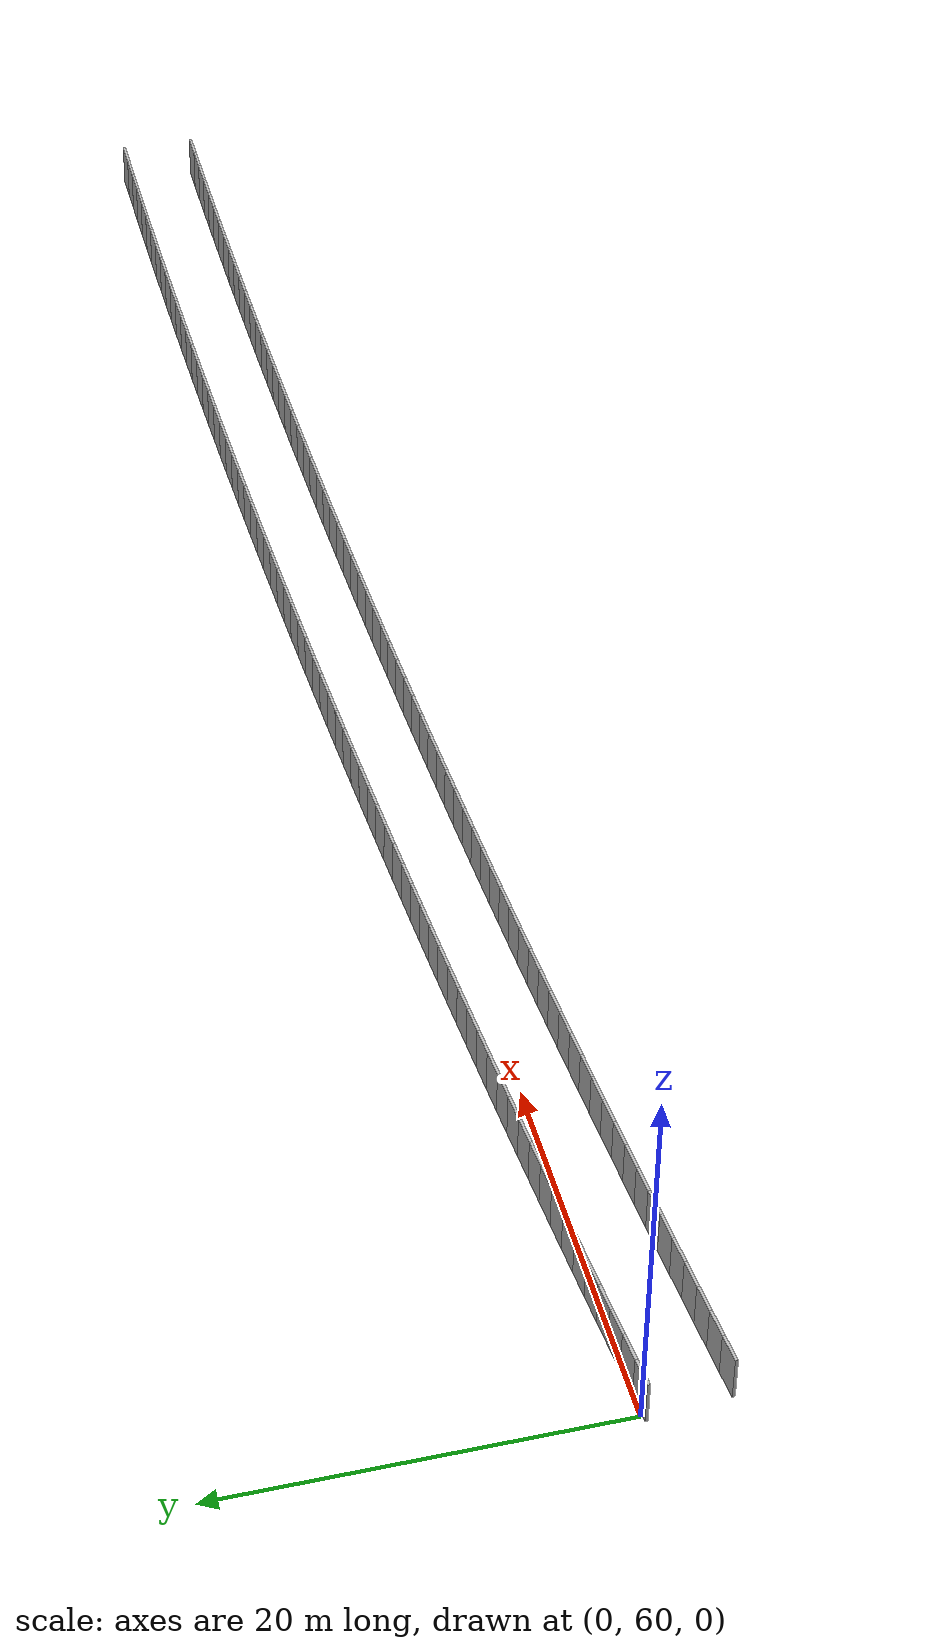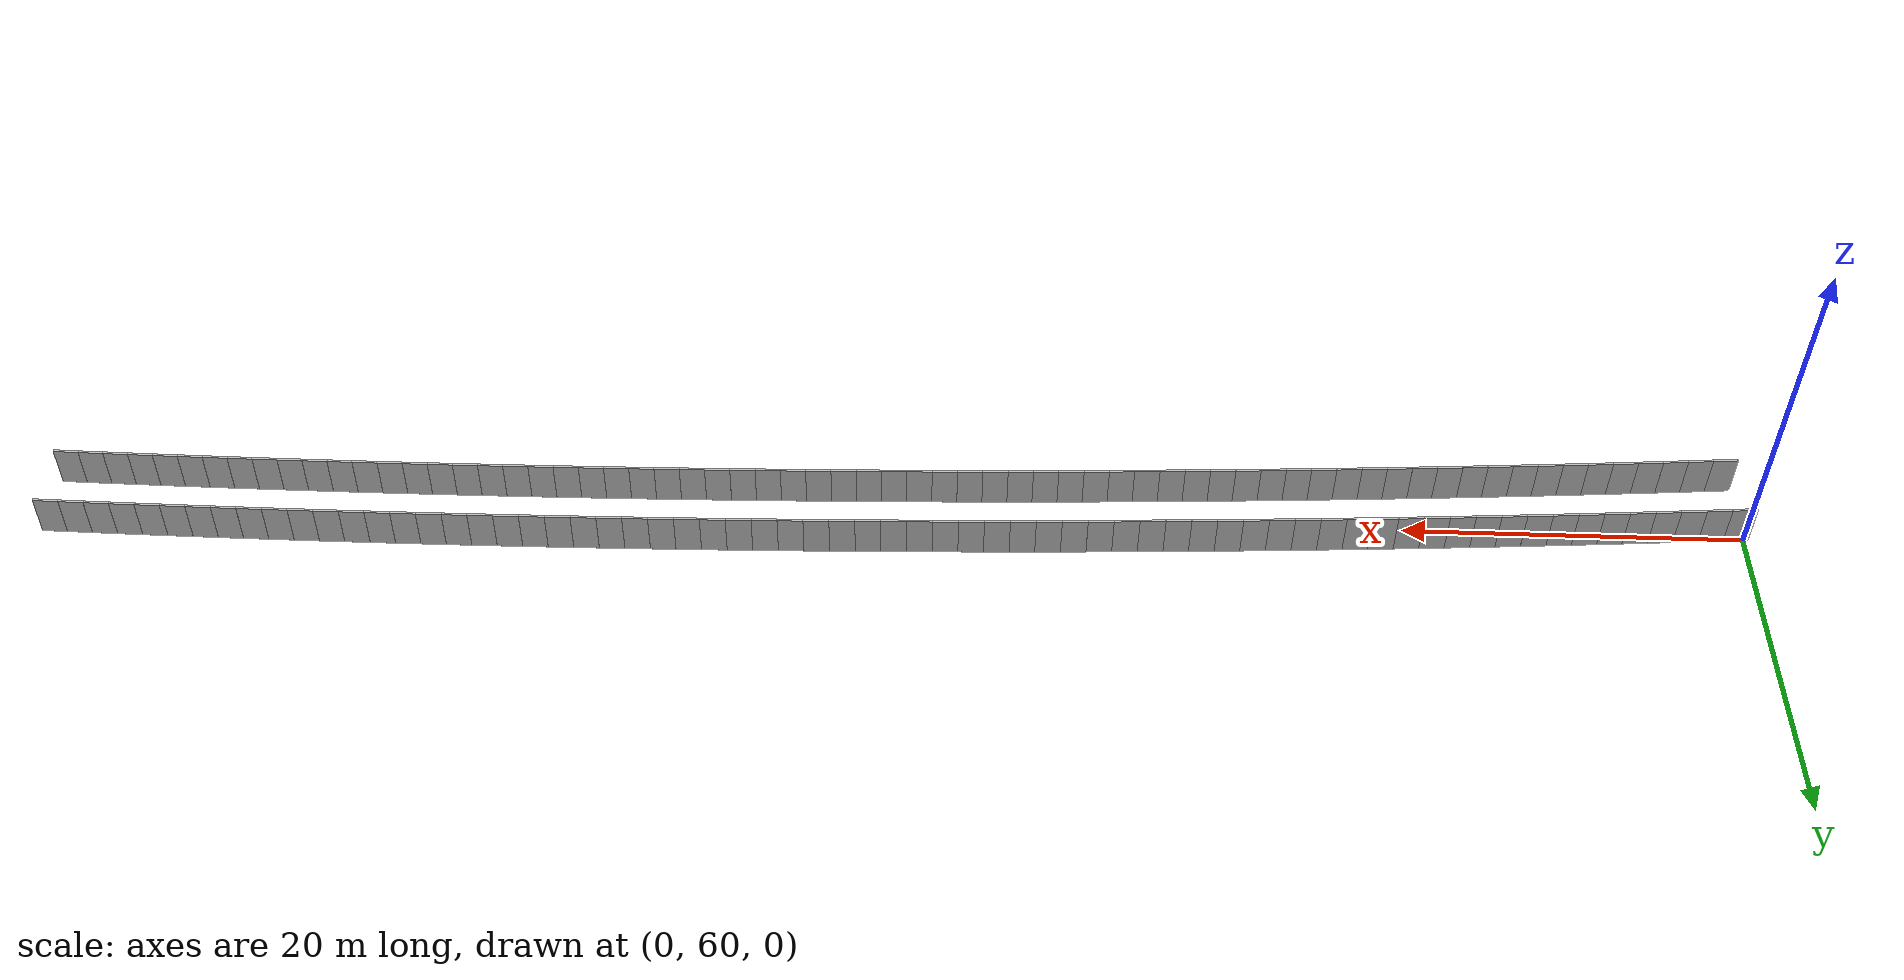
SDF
<?xml version="1.0" ?>
<sdf version="1.6">
  <model name="sps_1123">
    <pose frame="">0 0 0 0 -0 0</pose>
    <static>1</static>
    <self_collide>0</self_collide>
    <allow_auto_disable>0</allow_auto_disable>
    <link name="Wall2892">
      <kinematic>0</kinematic>
      <gravity>1</gravity>
      <self_collide>0</self_collide>
      <collision name="collision">
        <geometry>
          <box>
            <size>1.49664 0.15 2.5</size>
          </box>
        </geometry>
        <pose frame="">0 0 0 0 -0 0</pose>
      </collision>
      <visual name="visual">
        <geometry>
          <box>
            <size>1.49664 0.15 2.5</size>
          </box>
        </geometry>
        <pose frame="">0 0 0 0 -0 0</pose>
        <cast_shadows>1</cast_shadows>
        <transparency>0.0</transparency>
      </visual>
      <pose frame="">99.4662 59.1562 1.25 0 -0 3.12357</pose>
    </link>
    <link name="Wall2893">
      <kinematic>0</kinematic>
      <gravity>1</gravity>
      <self_collide>0</self_collide>
      <collision name="collision">
        <geometry>
          <box>
            <size>1.49636 0.15 2.5</size>
          </box>
        </geometry>
        <pose frame="">0 0 0 0 -0 0</pose>
      </collision>
      <visual name="visual">
        <geometry>
          <box>
            <size>1.49636 0.15 2.5</size>
          </box>
        </geometry>
        <pose frame="">0 0 0 0 -0 0</pose>
        <cast_shadows>1</cast_shadows>
        <transparency>0.0</transparency>
      </visual>
      <pose frame="">97.97 59.1821 1.25 0 -0 3.12503</pose>
    </link>
    <link name="Wall2894">
      <kinematic>0</kinematic>
      <gravity>1</gravity>
      <self_collide>0</self_collide>
      <collision name="collision">
        <geometry>
          <box>
            <size>1.49657 0.15 2.5</size>
          </box>
        </geometry>
        <pose frame="">0 0 0 0 -0 0</pose>
      </collision>
      <visual name="visual">
        <geometry>
          <box>
            <size>1.49657 0.15 2.5</size>
          </box>
        </geometry>
        <pose frame="">0 0 0 0 -0 0</pose>
        <cast_shadows>1</cast_shadows>
        <transparency>0.0</transparency>
      </visual>
      <pose frame="">96.4737 59.2057 1.25 0 -0 3.12662</pose>
    </link>
    <link name="Wall2895">
      <kinematic>0</kinematic>
      <gravity>1</gravity>
      <self_collide>0</self_collide>
      <collision name="collision">
        <geometry>
          <box>
            <size>1.49659 0.15 2.5</size>
          </box>
        </geometry>
        <pose frame="">0 0 0 0 -0 0</pose>
      </collision>
      <visual name="visual">
        <geometry>
          <box>
            <size>1.49659 0.15 2.5</size>
          </box>
        </geometry>
        <pose frame="">0 0 0 0 -0 0</pose>
        <cast_shadows>1</cast_shadows>
        <transparency>0.0</transparency>
      </visual>
      <pose frame="">94.9773 59.2268 1.25 0 -0 3.12834</pose>
    </link>
    <link name="Wall2896">
      <kinematic>0</kinematic>
      <gravity>1</gravity>
      <self_collide>0</self_collide>
      <collision name="collision">
        <geometry>
          <box>
            <size>1.4965 0.15 2.5</size>
          </box>
        </geometry>
        <pose frame="">0 0 0 0 -0 0</pose>
      </collision>
      <visual name="visual">
        <geometry>
          <box>
            <size>1.4965 0.15 2.5</size>
          </box>
        </geometry>
        <pose frame="">0 0 0 0 -0 0</pose>
        <cast_shadows>1</cast_shadows>
        <transparency>0.0</transparency>
      </visual>
      <pose frame="">93.4808 59.2455 1.25 0 -0 3.12985</pose>
    </link>
    <link name="Wall2897">
      <kinematic>0</kinematic>
      <gravity>1</gravity>
      <self_collide>0</self_collide>
      <collision name="collision">
        <geometry>
          <box>
            <size>1.49648 0.15 2.5</size>
          </box>
        </geometry>
        <pose frame="">0 0 0 0 -0 0</pose>
      </collision>
      <visual name="visual">
        <geometry>
          <box>
            <size>1.49648 0.15 2.5</size>
          </box>
        </geometry>
        <pose frame="">0 0 0 0 -0 0</pose>
        <cast_shadows>1</cast_shadows>
        <transparency>0.0</transparency>
      </visual>
      <pose frame="">91.9844 59.2619 1.25 0 -0 3.13144</pose>
    </link>
    <link name="Wall2898">
      <kinematic>0</kinematic>
      <gravity>1</gravity>
      <self_collide>0</self_collide>
      <collision name="collision">
        <geometry>
          <box>
            <size>1.49645 0.15 2.5</size>
          </box>
        </geometry>
        <pose frame="">0 0 0 0 -0 0</pose>
      </collision>
      <visual name="visual">
        <geometry>
          <box>
            <size>1.49645 0.15 2.5</size>
          </box>
        </geometry>
        <pose frame="">0 0 0 0 -0 0</pose>
        <cast_shadows>1</cast_shadows>
        <transparency>0.0</transparency>
      </visual>
      <pose frame="">90.488 59.2759 1.25 0 -0 3.13303</pose>
    </link>
    <link name="Wall2899">
      <kinematic>0</kinematic>
      <gravity>1</gravity>
      <self_collide>0</self_collide>
      <collision name="collision">
        <geometry>
          <box>
            <size>1.49643 0.15 2.5</size>
          </box>
        </geometry>
        <pose frame="">0 0 0 0 -0 0</pose>
      </collision>
      <visual name="visual">
        <geometry>
          <box>
            <size>1.49643 0.15 2.5</size>
          </box>
        </geometry>
        <pose frame="">0 0 0 0 -0 0</pose>
        <cast_shadows>1</cast_shadows>
        <transparency>0.0</transparency>
      </visual>
      <pose frame="">88.9916 59.2875 1.25 0 -0 3.13466</pose>
    </link>
    <link name="Wall2900">
      <kinematic>0</kinematic>
      <gravity>1</gravity>
      <self_collide>0</self_collide>
      <collision name="collision">
        <geometry>
          <box>
            <size>1.4966 0.15 2.5</size>
          </box>
        </geometry>
        <pose frame="">0 0 0 0 -0 0</pose>
      </collision>
      <visual name="visual">
        <geometry>
          <box>
            <size>1.4966 0.15 2.5</size>
          </box>
        </geometry>
        <pose frame="">0 0 0 0 -0 0</pose>
        <cast_shadows>1</cast_shadows>
        <transparency>0.0</transparency>
      </visual>
      <pose frame="">87.4951 59.2968 1.25 0 -0 3.13609</pose>
    </link>
    <link name="Wall2901">
      <kinematic>0</kinematic>
      <gravity>1</gravity>
      <self_collide>0</self_collide>
      <collision name="collision">
        <geometry>
          <box>
            <size>1.49641 0.15 2.5</size>
          </box>
        </geometry>
        <pose frame="">0 0 0 0 -0 0</pose>
      </collision>
      <visual name="visual">
        <geometry>
          <box>
            <size>1.49641 0.15 2.5</size>
          </box>
        </geometry>
        <pose frame="">0 0 0 0 -0 0</pose>
        <cast_shadows>1</cast_shadows>
        <transparency>0.0</transparency>
      </visual>
      <pose frame="">85.9986 59.3037 1.25 0 -0 3.13788</pose>
    </link>
    <link name="Wall2902">
      <kinematic>0</kinematic>
      <gravity>1</gravity>
      <self_collide>0</self_collide>
      <collision name="collision">
        <geometry>
          <box>
            <size>1.4964 0.15 2.5</size>
          </box>
        </geometry>
        <pose frame="">0 0 0 0 -0 0</pose>
      </collision>
      <visual name="visual">
        <geometry>
          <box>
            <size>1.4964 0.15 2.5</size>
          </box>
        </geometry>
        <pose frame="">0 0 0 0 -0 0</pose>
        <cast_shadows>1</cast_shadows>
        <transparency>0.0</transparency>
      </visual>
      <pose frame="">84.5023 59.3082 1.25 0 -0 3.13931</pose>
    </link>
    <link name="Wall2903">
      <kinematic>0</kinematic>
      <gravity>1</gravity>
      <self_collide>0</self_collide>
      <collision name="collision">
        <geometry>
          <box>
            <size>1.49658 0.15 2.5</size>
          </box>
        </geometry>
        <pose frame="">0 0 0 0 -0 0</pose>
      </collision>
      <visual name="visual">
        <geometry>
          <box>
            <size>1.49658 0.15 2.5</size>
          </box>
        </geometry>
        <pose frame="">0 0 0 0 -0 0</pose>
        <cast_shadows>1</cast_shadows>
        <transparency>0.0</transparency>
      </visual>
      <pose frame="">83.0058 59.3104 1.25 0 -0 3.14094</pose>
    </link>
    <link name="Wall2904">
      <kinematic>0</kinematic>
      <gravity>1</gravity>
      <self_collide>0</self_collide>
      <collision name="collision">
        <geometry>
          <box>
            <size>1.4964 0.15 2.5</size>
          </box>
        </geometry>
        <pose frame="">0 0 0 0 -0 0</pose>
      </collision>
      <visual name="visual">
        <geometry>
          <box>
            <size>1.4964 0.15 2.5</size>
          </box>
        </geometry>
        <pose frame="">0 0 0 0 -0 0</pose>
        <cast_shadows>1</cast_shadows>
        <transparency>0.0</transparency>
      </visual>
      <pose frame="">81.5093 59.3103 1.25 0 0 -3.14082</pose>
    </link>
    <link name="Wall2905">
      <kinematic>0</kinematic>
      <gravity>1</gravity>
      <self_collide>0</self_collide>
      <collision name="collision">
        <geometry>
          <box>
            <size>1.49665 0.15 2.5</size>
          </box>
        </geometry>
        <pose frame="">0 0 0 0 -0 0</pose>
      </collision>
      <visual name="visual">
        <geometry>
          <box>
            <size>1.49665 0.15 2.5</size>
          </box>
        </geometry>
        <pose frame="">0 0 0 0 -0 0</pose>
        <cast_shadows>1</cast_shadows>
        <transparency>0.0</transparency>
      </visual>
      <pose frame="">80.0127 59.3078 1.25 0 0 -3.13906</pose>
    </link>
    <link name="Wall2906">
      <kinematic>0</kinematic>
      <gravity>1</gravity>
      <self_collide>0</self_collide>
      <collision name="collision">
        <geometry>
          <box>
            <size>1.49659 0.15 2.5</size>
          </box>
        </geometry>
        <pose frame="">0 0 0 0 -0 0</pose>
      </collision>
      <visual name="visual">
        <geometry>
          <box>
            <size>1.49659 0.15 2.5</size>
          </box>
        </geometry>
        <pose frame="">0 0 0 0 -0 0</pose>
        <cast_shadows>1</cast_shadows>
        <transparency>0.0</transparency>
      </visual>
      <pose frame="">78.5161 59.3028 1.25 0 0 -3.13743</pose>
    </link>
    <link name="Wall2907">
      <kinematic>0</kinematic>
      <gravity>1</gravity>
      <self_collide>0</self_collide>
      <collision name="collision">
        <geometry>
          <box>
            <size>1.49642 0.15 2.5</size>
          </box>
        </geometry>
        <pose frame="">0 0 0 0 -0 0</pose>
      </collision>
      <visual name="visual">
        <geometry>
          <box>
            <size>1.49642 0.15 2.5</size>
          </box>
        </geometry>
        <pose frame="">0 0 0 0 -0 0</pose>
        <cast_shadows>1</cast_shadows>
        <transparency>0.0</transparency>
      </visual>
      <pose frame="">77.0196 59.2955 1.25 0 0 -3.13596</pose>
    </link>
    <link name="Wall2908">
      <kinematic>0</kinematic>
      <gravity>1</gravity>
      <self_collide>0</self_collide>
      <collision name="collision">
        <geometry>
          <box>
            <size>1.49644 0.15 2.5</size>
          </box>
        </geometry>
        <pose frame="">0 0 0 0 -0 0</pose>
      </collision>
      <visual name="visual">
        <geometry>
          <box>
            <size>1.49644 0.15 2.5</size>
          </box>
        </geometry>
        <pose frame="">0 0 0 0 -0 0</pose>
        <cast_shadows>1</cast_shadows>
        <transparency>0.0</transparency>
      </visual>
      <pose frame="">75.5232 59.2858 1.25 0 0 -3.13425</pose>
    </link>
    <link name="Wall2909">
      <kinematic>0</kinematic>
      <gravity>1</gravity>
      <self_collide>0</self_collide>
      <collision name="collision">
        <geometry>
          <box>
            <size>1.49664 0.15 2.5</size>
          </box>
        </geometry>
        <pose frame="">0 0 0 0 -0 0</pose>
      </collision>
      <visual name="visual">
        <geometry>
          <box>
            <size>1.49664 0.15 2.5</size>
          </box>
        </geometry>
        <pose frame="">0 0 0 0 -0 0</pose>
        <cast_shadows>1</cast_shadows>
        <transparency>0.0</transparency>
      </visual>
      <pose frame="">74.0268 59.2737 1.25 0 0 -3.13278</pose>
    </link>
    <link name="Wall2910">
      <kinematic>0</kinematic>
      <gravity>1</gravity>
      <self_collide>0</self_collide>
      <collision name="collision">
        <geometry>
          <box>
            <size>1.49648 0.15 2.5</size>
          </box>
        </geometry>
        <pose frame="">0 0 0 0 -0 0</pose>
      </collision>
      <visual name="visual">
        <geometry>
          <box>
            <size>1.49648 0.15 2.5</size>
          </box>
        </geometry>
        <pose frame="">0 0 0 0 -0 0</pose>
        <cast_shadows>1</cast_shadows>
        <transparency>0.0</transparency>
      </visual>
      <pose frame="">72.5303 59.2593 1.25 0 0 -3.13115</pose>
    </link>
    <link name="Wall2911">
      <kinematic>0</kinematic>
      <gravity>1</gravity>
      <self_collide>0</self_collide>
      <collision name="collision">
        <geometry>
          <box>
            <size>1.49651 0.15 2.5</size>
          </box>
        </geometry>
        <pose frame="">0 0 0 0 -0 0</pose>
      </collision>
      <visual name="visual">
        <geometry>
          <box>
            <size>1.49651 0.15 2.5</size>
          </box>
        </geometry>
        <pose frame="">0 0 0 0 -0 0</pose>
        <cast_shadows>1</cast_shadows>
        <transparency>0.0</transparency>
      </visual>
      <pose frame="">71.0339 59.2425 1.25 0 0 -3.12956</pose>
    </link>
    <link name="Wall2912">
      <kinematic>0</kinematic>
      <gravity>1</gravity>
      <self_collide>0</self_collide>
      <collision name="collision">
        <geometry>
          <box>
            <size>1.49635 0.15 2.5</size>
          </box>
        </geometry>
        <pose frame="">0 0 0 0 -0 0</pose>
      </collision>
      <visual name="visual">
        <geometry>
          <box>
            <size>1.49635 0.15 2.5</size>
          </box>
        </geometry>
        <pose frame="">0 0 0 0 -0 0</pose>
        <cast_shadows>1</cast_shadows>
        <transparency>0.0</transparency>
      </visual>
      <pose frame="">69.5376 59.2233 1.25 0 0 -3.12797</pose>
    </link>
    <link name="Wall2913">
      <kinematic>0</kinematic>
      <gravity>1</gravity>
      <self_collide>0</self_collide>
      <collision name="collision">
        <geometry>
          <box>
            <size>1.49657 0.15 2.5</size>
          </box>
        </geometry>
        <pose frame="">0 0 0 0 -0 0</pose>
      </collision>
      <visual name="visual">
        <geometry>
          <box>
            <size>1.49657 0.15 2.5</size>
          </box>
        </geometry>
        <pose frame="">0 0 0 0 -0 0</pose>
        <cast_shadows>1</cast_shadows>
        <transparency>0.0</transparency>
      </visual>
      <pose frame="">68.0413 59.2017 1.25 0 0 -3.12638</pose>
    </link>
    <link name="Wall2914">
      <kinematic>0</kinematic>
      <gravity>1</gravity>
      <self_collide>0</self_collide>
      <collision name="collision">
        <geometry>
          <box>
            <size>1.49661 0.15 2.5</size>
          </box>
        </geometry>
        <pose frame="">0 0 0 0 -0 0</pose>
      </collision>
      <visual name="visual">
        <geometry>
          <box>
            <size>1.49661 0.15 2.5</size>
          </box>
        </geometry>
        <pose frame="">0 0 0 0 -0 0</pose>
        <cast_shadows>1</cast_shadows>
        <transparency>0.0</transparency>
      </visual>
      <pose frame="">66.5449 59.1778 1.25 0 0 -3.12487</pose>
    </link>
    <link name="Wall2915">
      <kinematic>0</kinematic>
      <gravity>1</gravity>
      <self_collide>0</self_collide>
      <collision name="collision">
        <geometry>
          <box>
            <size>1.49647 0.15 2.5</size>
          </box>
        </geometry>
        <pose frame="">0 0 0 0 -0 0</pose>
      </collision>
      <visual name="visual">
        <geometry>
          <box>
            <size>1.49647 0.15 2.5</size>
          </box>
        </geometry>
        <pose frame="">0 0 0 0 -0 0</pose>
        <cast_shadows>1</cast_shadows>
        <transparency>0.0</transparency>
      </visual>
      <pose frame="">65.0485 59.1515 1.25 0 0 -3.12316</pose>
    </link>
    <link name="Wall2916">
      <kinematic>0</kinematic>
      <gravity>1</gravity>
      <self_collide>0</self_collide>
      <collision name="collision">
        <geometry>
          <box>
            <size>1.49645 0.15 2.5</size>
          </box>
        </geometry>
        <pose frame="">0 0 0 0 -0 0</pose>
      </collision>
      <visual name="visual">
        <geometry>
          <box>
            <size>1.49645 0.15 2.5</size>
          </box>
        </geometry>
        <pose frame="">0 0 0 0 -0 0</pose>
        <cast_shadows>1</cast_shadows>
        <transparency>0.0</transparency>
      </visual>
      <pose frame="">63.5524 59.1228 1.25 0 0 -3.12165</pose>
    </link>
    <link name="Wall2917">
      <kinematic>0</kinematic>
      <gravity>1</gravity>
      <self_collide>0</self_collide>
      <collision name="collision">
        <geometry>
          <box>
            <size>1.49656 0.15 2.5</size>
          </box>
        </geometry>
        <pose frame="">0 0 0 0 -0 0</pose>
      </collision>
      <visual name="visual">
        <geometry>
          <box>
            <size>1.49656 0.15 2.5</size>
          </box>
        </geometry>
        <pose frame="">0 0 0 0 -0 0</pose>
        <cast_shadows>1</cast_shadows>
        <transparency>0.0</transparency>
      </visual>
      <pose frame="">62.0562 59.0918 1.25 0 0 -3.1201</pose>
    </link>
    <link name="Wall2918">
      <kinematic>0</kinematic>
      <gravity>1</gravity>
      <self_collide>0</self_collide>
      <collision name="collision">
        <geometry>
          <box>
            <size>1.49643 0.15 2.5</size>
          </box>
        </geometry>
        <pose frame="">0 0 0 0 -0 0</pose>
      </collision>
      <visual name="visual">
        <geometry>
          <box>
            <size>1.49643 0.15 2.5</size>
          </box>
        </geometry>
        <pose frame="">0 0 0 0 -0 0</pose>
        <cast_shadows>1</cast_shadows>
        <transparency>0.0</transparency>
      </visual>
      <pose frame="">60.5601 59.0584 1.25 0 0 -3.11846</pose>
    </link>
    <link name="Wall2919">
      <kinematic>0</kinematic>
      <gravity>1</gravity>
      <self_collide>0</self_collide>
      <collision name="collision">
        <geometry>
          <box>
            <size>1.49643 0.15 2.5</size>
          </box>
        </geometry>
        <pose frame="">0 0 0 0 -0 0</pose>
      </collision>
      <visual name="visual">
        <geometry>
          <box>
            <size>1.49643 0.15 2.5</size>
          </box>
        </geometry>
        <pose frame="">0 0 0 0 -0 0</pose>
        <cast_shadows>1</cast_shadows>
        <transparency>0.0</transparency>
      </visual>
      <pose frame="">59.064 59.0226 1.25 0 0 -3.11687</pose>
    </link>
    <link name="Wall2920">
      <kinematic>0</kinematic>
      <gravity>1</gravity>
      <self_collide>0</self_collide>
      <collision name="collision">
        <geometry>
          <box>
            <size>1.49655 0.15 2.5</size>
          </box>
        </geometry>
        <pose frame="">0 0 0 0 -0 0</pose>
      </collision>
      <visual name="visual">
        <geometry>
          <box>
            <size>1.49655 0.15 2.5</size>
          </box>
        </geometry>
        <pose frame="">0 0 0 0 -0 0</pose>
        <cast_shadows>1</cast_shadows>
        <transparency>0.0</transparency>
      </visual>
      <pose frame="">57.568 58.9845 1.25 0 0 -3.11541</pose>
    </link>
    <link name="Wall2921">
      <kinematic>0</kinematic>
      <gravity>1</gravity>
      <self_collide>0</self_collide>
      <collision name="collision">
        <geometry>
          <box>
            <size>1.49637 0.15 2.5</size>
          </box>
        </geometry>
        <pose frame="">0 0 0 0 -0 0</pose>
      </collision>
      <visual name="visual">
        <geometry>
          <box>
            <size>1.49637 0.15 2.5</size>
          </box>
        </geometry>
        <pose frame="">0 0 0 0 -0 0</pose>
        <cast_shadows>1</cast_shadows>
        <transparency>0.0</transparency>
      </visual>
      <pose frame="">56.0721 58.9441 1.25 0 0 -3.11377</pose>
    </link>
    <link name="Wall2922">
      <kinematic>0</kinematic>
      <gravity>1</gravity>
      <self_collide>0</self_collide>
      <collision name="collision">
        <geometry>
          <box>
            <size>1.49644 0.15 2.5</size>
          </box>
        </geometry>
        <pose frame="">0 0 0 0 -0 0</pose>
      </collision>
      <visual name="visual">
        <geometry>
          <box>
            <size>1.49644 0.15 2.5</size>
          </box>
        </geometry>
        <pose frame="">0 0 0 0 -0 0</pose>
        <cast_shadows>1</cast_shadows>
        <transparency>0.0</transparency>
      </visual>
      <pose frame="">54.5763 58.9013 1.25 0 0 -3.11218</pose>
    </link>
    <link name="Wall2923">
      <kinematic>0</kinematic>
      <gravity>1</gravity>
      <self_collide>0</self_collide>
      <collision name="collision">
        <geometry>
          <box>
            <size>1.49651 0.15 2.5</size>
          </box>
        </geometry>
        <pose frame="">0 0 0 0 -0 0</pose>
      </collision>
      <visual name="visual">
        <geometry>
          <box>
            <size>1.49651 0.15 2.5</size>
          </box>
        </geometry>
        <pose frame="">0 0 0 0 -0 0</pose>
        <cast_shadows>1</cast_shadows>
        <transparency>0.0</transparency>
      </visual>
      <pose frame="">53.0806 58.856 1.25 0 0 -3.11047</pose>
    </link>
    <link name="Wall2924">
      <kinematic>0</kinematic>
      <gravity>1</gravity>
      <self_collide>0</self_collide>
      <collision name="collision">
        <geometry>
          <box>
            <size>1.49659 0.15 2.5</size>
          </box>
        </geometry>
        <pose frame="">0 0 0 0 -0 0</pose>
      </collision>
      <visual name="visual">
        <geometry>
          <box>
            <size>1.49659 0.15 2.5</size>
          </box>
        </geometry>
        <pose frame="">0 0 0 0 -0 0</pose>
        <cast_shadows>1</cast_shadows>
        <transparency>0.0</transparency>
      </visual>
      <pose frame="">51.5848 58.8083 1.25 0 0 -3.10896</pose>
    </link>
    <link name="Wall2925">
      <kinematic>0</kinematic>
      <gravity>1</gravity>
      <self_collide>0</self_collide>
      <collision name="collision">
        <geometry>
          <box>
            <size>1.49673 0.15 2.5</size>
          </box>
        </geometry>
        <pose frame="">0 0 0 0 -0 0</pose>
      </collision>
      <visual name="visual">
        <geometry>
          <box>
            <size>1.49673 0.15 2.5</size>
          </box>
        </geometry>
        <pose frame="">0 0 0 0 -0 0</pose>
        <cast_shadows>1</cast_shadows>
        <transparency>0.0</transparency>
      </visual>
      <pose frame="">50.089 58.7583 1.25 0 0 -3.10737</pose>
    </link>
    <link name="Wall2926">
      <kinematic>0</kinematic>
      <gravity>1</gravity>
      <self_collide>0</self_collide>
      <collision name="collision">
        <geometry>
          <box>
            <size>1.49631 0.15 2.5</size>
          </box>
        </geometry>
        <pose frame="">0 0 0 0 -0 0</pose>
      </collision>
      <visual name="visual">
        <geometry>
          <box>
            <size>1.49631 0.15 2.5</size>
          </box>
        </geometry>
        <pose frame="">0 0 0 0 -0 0</pose>
        <cast_shadows>1</cast_shadows>
        <transparency>0.0</transparency>
      </visual>
      <pose frame="">48.5933 58.706 1.25 0 0 -3.10589</pose>
    </link>
    <link name="Wall2927">
      <kinematic>0</kinematic>
      <gravity>1</gravity>
      <self_collide>0</self_collide>
      <collision name="collision">
        <geometry>
          <box>
            <size>1.49647 0.15 2.5</size>
          </box>
        </geometry>
        <pose frame="">0 0 0 0 -0 0</pose>
      </collision>
      <visual name="visual">
        <geometry>
          <box>
            <size>1.49647 0.15 2.5</size>
          </box>
        </geometry>
        <pose frame="">0 0 0 0 -0 0</pose>
        <cast_shadows>1</cast_shadows>
        <transparency>0.0</transparency>
      </visual>
      <pose frame="">47.098 58.6513 1.25 0 0 -3.10418</pose>
    </link>
    <link name="Wall2928">
      <kinematic>0</kinematic>
      <gravity>1</gravity>
      <self_collide>0</self_collide>
      <collision name="collision">
        <geometry>
          <box>
            <size>1.49649 0.15 2.5</size>
          </box>
        </geometry>
        <pose frame="">0 0 0 0 -0 0</pose>
      </collision>
      <visual name="visual">
        <geometry>
          <box>
            <size>1.49649 0.15 2.5</size>
          </box>
        </geometry>
        <pose frame="">0 0 0 0 -0 0</pose>
        <cast_shadows>1</cast_shadows>
        <transparency>0.0</transparency>
      </visual>
      <pose frame="">45.6026 58.5942 1.25 0 0 -3.10267</pose>
    </link>
    <link name="Wall2929">
      <kinematic>0</kinematic>
      <gravity>1</gravity>
      <self_collide>0</self_collide>
      <collision name="collision">
        <geometry>
          <box>
            <size>1.49647 0.15 2.5</size>
          </box>
        </geometry>
        <pose frame="">0 0 0 0 -0 0</pose>
      </collision>
      <visual name="visual">
        <geometry>
          <box>
            <size>1.49647 0.15 2.5</size>
          </box>
        </geometry>
        <pose frame="">0 0 0 0 -0 0</pose>
        <cast_shadows>1</cast_shadows>
        <transparency>0.0</transparency>
      </visual>
      <pose frame="">44.1073 58.5348 1.25 0 0 -3.10108</pose>
    </link>
    <link name="Wall2930">
      <kinematic>0</kinematic>
      <gravity>1</gravity>
      <self_collide>0</self_collide>
      <collision name="collision">
        <geometry>
          <box>
            <size>1.4965 0.15 2.5</size>
          </box>
        </geometry>
        <pose frame="">0 0 0 0 -0 0</pose>
      </collision>
      <visual name="visual">
        <geometry>
          <box>
            <size>1.4965 0.15 2.5</size>
          </box>
        </geometry>
        <pose frame="">0 0 0 0 -0 0</pose>
        <cast_shadows>1</cast_shadows>
        <transparency>0.0</transparency>
      </visual>
      <pose frame="">42.6121 58.473 1.25 0 0 -3.09949</pose>
    </link>
    <link name="Wall2931">
      <kinematic>0</kinematic>
      <gravity>1</gravity>
      <self_collide>0</self_collide>
      <collision name="collision">
        <geometry>
          <box>
            <size>1.49642 0.15 2.5</size>
          </box>
        </geometry>
        <pose frame="">0 0 0 0 -0 0</pose>
      </collision>
      <visual name="visual">
        <geometry>
          <box>
            <size>1.49642 0.15 2.5</size>
          </box>
        </geometry>
        <pose frame="">0 0 0 0 -0 0</pose>
        <cast_shadows>1</cast_shadows>
        <transparency>0.0</transparency>
      </visual>
      <pose frame="">41.117 58.4088 1.25 0 0 -3.0979</pose>
    </link>
    <link name="Wall2932">
      <kinematic>0</kinematic>
      <gravity>1</gravity>
      <self_collide>0</self_collide>
      <collision name="collision">
        <geometry>
          <box>
            <size>1.49653 0.15 2.5</size>
          </box>
        </geometry>
        <pose frame="">0 0 0 0 -0 0</pose>
      </collision>
      <visual name="visual">
        <geometry>
          <box>
            <size>1.49653 0.15 2.5</size>
          </box>
        </geometry>
        <pose frame="">0 0 0 0 -0 0</pose>
        <cast_shadows>1</cast_shadows>
        <transparency>0.0</transparency>
      </visual>
      <pose frame="">39.622 58.3422 1.25 0 0 -3.09627</pose>
    </link>
    <link name="Wall2933">
      <kinematic>0</kinematic>
      <gravity>1</gravity>
      <self_collide>0</self_collide>
      <collision name="collision">
        <geometry>
          <box>
            <size>1.49664 0.15 2.5</size>
          </box>
        </geometry>
        <pose frame="">0 0 0 0 -0 0</pose>
      </collision>
      <visual name="visual">
        <geometry>
          <box>
            <size>1.49664 0.15 2.5</size>
          </box>
        </geometry>
        <pose frame="">0 0 0 0 -0 0</pose>
        <cast_shadows>1</cast_shadows>
        <transparency>0.0</transparency>
      </visual>
      <pose frame="">38.127 58.2732 1.25 0 0 -3.09468</pose>
    </link>
    <link name="Wall2934">
      <kinematic>0</kinematic>
      <gravity>1</gravity>
      <self_collide>0</self_collide>
      <collision name="collision">
        <geometry>
          <box>
            <size>1.49638 0.15 2.5</size>
          </box>
        </geometry>
        <pose frame="">0 0 0 0 -0 0</pose>
      </collision>
      <visual name="visual">
        <geometry>
          <box>
            <size>1.49638 0.15 2.5</size>
          </box>
        </geometry>
        <pose frame="">0 0 0 0 -0 0</pose>
        <cast_shadows>1</cast_shadows>
        <transparency>0.0</transparency>
      </visual>
      <pose frame="">36.6322 58.2019 1.25 0 0 -3.09316</pose>
    </link>
    <link name="Wall2935">
      <kinematic>0</kinematic>
      <gravity>1</gravity>
      <self_collide>0</self_collide>
      <collision name="collision">
        <geometry>
          <box>
            <size>1.49668 0.15 2.5</size>
          </box>
        </geometry>
        <pose frame="">0 0 0 0 -0 0</pose>
      </collision>
      <visual name="visual">
        <geometry>
          <box>
            <size>1.49668 0.15 2.5</size>
          </box>
        </geometry>
        <pose frame="">0 0 0 0 -0 0</pose>
        <cast_shadows>1</cast_shadows>
        <transparency>0.0</transparency>
      </visual>
      <pose frame="">35.1374 58.1283 1.25 0 0 -3.09162</pose>
    </link>
    <link name="Wall2936">
      <kinematic>0</kinematic>
      <gravity>1</gravity>
      <self_collide>0</self_collide>
      <collision name="collision">
        <geometry>
          <box>
            <size>1.49638 0.15 2.5</size>
          </box>
        </geometry>
        <pose frame="">0 0 0 0 -0 0</pose>
      </collision>
      <visual name="visual">
        <geometry>
          <box>
            <size>1.49638 0.15 2.5</size>
          </box>
        </geometry>
        <pose frame="">0 0 0 0 -0 0</pose>
        <cast_shadows>1</cast_shadows>
        <transparency>0.0</transparency>
      </visual>
      <pose frame="">33.6428 58.0523 1.25 0 0 -3.08997</pose>
    </link>
    <link name="Wall2937">
      <kinematic>0</kinematic>
      <gravity>1</gravity>
      <self_collide>0</self_collide>
      <collision name="collision">
        <geometry>
          <box>
            <size>1.4965 0.15 2.5</size>
          </box>
        </geometry>
        <pose frame="">0 0 0 0 -0 0</pose>
      </collision>
      <visual name="visual">
        <geometry>
          <box>
            <size>1.4965 0.15 2.5</size>
          </box>
        </geometry>
        <pose frame="">0 0 0 0 -0 0</pose>
        <cast_shadows>1</cast_shadows>
        <transparency>0.0</transparency>
      </visual>
      <pose frame="">32.1485 57.9739 1.25 0 0 -3.08838</pose>
    </link>
    <link name="Wall2938">
      <kinematic>0</kinematic>
      <gravity>1</gravity>
      <self_collide>0</self_collide>
      <collision name="collision">
        <geometry>
          <box>
            <size>1.49663 0.15 2.5</size>
          </box>
        </geometry>
        <pose frame="">0 0 0 0 -0 0</pose>
      </collision>
      <visual name="visual">
        <geometry>
          <box>
            <size>1.49663 0.15 2.5</size>
          </box>
        </geometry>
        <pose frame="">0 0 0 0 -0 0</pose>
        <cast_shadows>1</cast_shadows>
        <transparency>0.0</transparency>
      </visual>
      <pose frame="">30.6541 57.8931 1.25 0 0 -3.08675</pose>
    </link>
    <link name="Wall2939">
      <kinematic>0</kinematic>
      <gravity>1</gravity>
      <self_collide>0</self_collide>
      <collision name="collision">
        <geometry>
          <box>
            <size>1.4964 0.15 2.5</size>
          </box>
        </geometry>
        <pose frame="">0 0 0 0 -0 0</pose>
      </collision>
      <visual name="visual">
        <geometry>
          <box>
            <size>1.4964 0.15 2.5</size>
          </box>
        </geometry>
        <pose frame="">0 0 0 0 -0 0</pose>
        <cast_shadows>1</cast_shadows>
        <transparency>0.0</transparency>
      </visual>
      <pose frame="">29.1599 57.8099 1.25 0 0 -3.08519</pose>
    </link>
    <link name="Wall2940">
      <kinematic>0</kinematic>
      <gravity>1</gravity>
      <self_collide>0</self_collide>
      <collision name="collision">
        <geometry>
          <box>
            <size>1.49653 0.15 2.5</size>
          </box>
        </geometry>
        <pose frame="">0 0 0 0 -0 0</pose>
      </collision>
      <visual name="visual">
        <geometry>
          <box>
            <size>1.49653 0.15 2.5</size>
          </box>
        </geometry>
        <pose frame="">0 0 0 0 -0 0</pose>
        <cast_shadows>1</cast_shadows>
        <transparency>0.0</transparency>
      </visual>
      <pose frame="">27.6659 57.7244 1.25 0 0 -3.08369</pose>
    </link>
    <link name="Wall2941">
      <kinematic>0</kinematic>
      <gravity>1</gravity>
      <self_collide>0</self_collide>
      <collision name="collision">
        <geometry>
          <box>
            <size>1.49644 0.15 2.5</size>
          </box>
        </geometry>
        <pose frame="">0 0 0 0 -0 0</pose>
      </collision>
      <visual name="visual">
        <geometry>
          <box>
            <size>1.49644 0.15 2.5</size>
          </box>
        </geometry>
        <pose frame="">0 0 0 0 -0 0</pose>
        <cast_shadows>1</cast_shadows>
        <transparency>0.0</transparency>
      </visual>
      <pose frame="">26.172 57.6365 1.25 0 0 -3.08193</pose>
    </link>
    <link name="Wall2942">
      <kinematic>0</kinematic>
      <gravity>1</gravity>
      <self_collide>0</self_collide>
      <collision name="collision">
        <geometry>
          <box>
            <size>1.49662 0.15 2.5</size>
          </box>
        </geometry>
        <pose frame="">0 0 0 0 -0 0</pose>
      </collision>
      <visual name="visual">
        <geometry>
          <box>
            <size>1.49662 0.15 2.5</size>
          </box>
        </geometry>
        <pose frame="">0 0 0 0 -0 0</pose>
        <cast_shadows>1</cast_shadows>
        <transparency>0.0</transparency>
      </visual>
      <pose frame="">24.6782 57.5463 1.25 0 0 -3.08063</pose>
    </link>
    <link name="Wall2943">
      <kinematic>0</kinematic>
      <gravity>1</gravity>
      <self_collide>0</self_collide>
      <collision name="collision">
        <geometry>
          <box>
            <size>1.49635 0.15 2.5</size>
          </box>
        </geometry>
        <pose frame="">0 0 0 0 -0 0</pose>
      </collision>
      <visual name="visual">
        <geometry>
          <box>
            <size>1.49635 0.15 2.5</size>
          </box>
        </geometry>
        <pose frame="">0 0 0 0 -0 0</pose>
        <cast_shadows>1</cast_shadows>
        <transparency>0.0</transparency>
      </visual>
      <pose frame="">23.1845 57.4538 1.25 0 0 -3.07886</pose>
    </link>
    <link name="Wall2944">
      <kinematic>0</kinematic>
      <gravity>1</gravity>
      <self_collide>0</self_collide>
      <collision name="collision">
        <geometry>
          <box>
            <size>1.49644 0.15 2.5</size>
          </box>
        </geometry>
        <pose frame="">0 0 0 0 -0 0</pose>
      </collision>
      <visual name="visual">
        <geometry>
          <box>
            <size>1.49644 0.15 2.5</size>
          </box>
        </geometry>
        <pose frame="">0 0 0 0 -0 0</pose>
        <cast_shadows>1</cast_shadows>
        <transparency>0.0</transparency>
      </visual>
      <pose frame="">21.6912 57.3588 1.25 0 0 -3.07727</pose>
    </link>
    <link name="Wall2945">
      <kinematic>0</kinematic>
      <gravity>1</gravity>
      <self_collide>0</self_collide>
      <collision name="collision">
        <geometry>
          <box>
            <size>1.49648 0.15 2.5</size>
          </box>
        </geometry>
        <pose frame="">0 0 0 0 -0 0</pose>
      </collision>
      <visual name="visual">
        <geometry>
          <box>
            <size>1.49648 0.15 2.5</size>
          </box>
        </geometry>
        <pose frame="">0 0 0 0 -0 0</pose>
        <cast_shadows>1</cast_shadows>
        <transparency>0.0</transparency>
      </visual>
      <pose frame="">20.1979 57.2614 1.25 0 0 -3.07568</pose>
    </link>
    <link name="Wall2946">
      <kinematic>0</kinematic>
      <gravity>1</gravity>
      <self_collide>0</self_collide>
      <collision name="collision">
        <geometry>
          <box>
            <size>1.49663 0.15 2.5</size>
          </box>
        </geometry>
        <pose frame="">0 0 0 0 -0 0</pose>
      </collision>
      <visual name="visual">
        <geometry>
          <box>
            <size>1.49663 0.15 2.5</size>
          </box>
        </geometry>
        <pose frame="">0 0 0 0 -0 0</pose>
        <cast_shadows>1</cast_shadows>
        <transparency>0.0</transparency>
      </visual>
      <pose frame="">18.7046 57.1617 1.25 0 0 -3.07417</pose>
    </link>
    <link name="Wall2947">
      <kinematic>0</kinematic>
      <gravity>1</gravity>
      <self_collide>0</self_collide>
      <collision name="collision">
        <geometry>
          <box>
            <size>1.49637 0.15 2.5</size>
          </box>
        </geometry>
        <pose frame="">0 0 0 0 -0 0</pose>
      </collision>
      <visual name="visual">
        <geometry>
          <box>
            <size>1.49637 0.15 2.5</size>
          </box>
        </geometry>
        <pose frame="">0 0 0 0 -0 0</pose>
        <cast_shadows>1</cast_shadows>
        <transparency>0.0</transparency>
      </visual>
      <pose frame="">17.2116 57.0596 1.25 0 0 -3.07244</pose>
    </link>
    <link name="Wall2948">
      <kinematic>0</kinematic>
      <gravity>1</gravity>
      <self_collide>0</self_collide>
      <collision name="collision">
        <geometry>
          <box>
            <size>1.49653 0.15 2.5</size>
          </box>
        </geometry>
        <pose frame="">0 0 0 0 -0 0</pose>
      </collision>
      <visual name="visual">
        <geometry>
          <box>
            <size>1.49653 0.15 2.5</size>
          </box>
        </geometry>
        <pose frame="">0 0 0 0 -0 0</pose>
        <cast_shadows>1</cast_shadows>
        <transparency>0.0</transparency>
      </visual>
      <pose frame="">15.7188 56.9551 1.25 0 0 -3.07098</pose>
    </link>
    <link name="Wall2949">
      <kinematic>0</kinematic>
      <gravity>1</gravity>
      <self_collide>0</self_collide>
      <collision name="collision">
        <geometry>
          <box>
            <size>1.49672 0.15 2.5</size>
          </box>
        </geometry>
        <pose frame="">0 0 0 0 -0 0</pose>
      </collision>
      <visual name="visual">
        <geometry>
          <box>
            <size>1.49672 0.15 2.5</size>
          </box>
        </geometry>
        <pose frame="">0 0 0 0 -0 0</pose>
        <cast_shadows>1</cast_shadows>
        <transparency>0.0</transparency>
      </visual>
      <pose frame="">14.226 56.8482 1.25 0 0 -3.06923</pose>
    </link>
    <link name="Wall2950">
      <kinematic>0</kinematic>
      <gravity>1</gravity>
      <self_collide>0</self_collide>
      <collision name="collision">
        <geometry>
          <box>
            <size>1.49643 0.15 2.5</size>
          </box>
        </geometry>
        <pose frame="">0 0 0 0 -0 0</pose>
      </collision>
      <visual name="visual">
        <geometry>
          <box>
            <size>1.49643 0.15 2.5</size>
          </box>
        </geometry>
        <pose frame="">0 0 0 0 -0 0</pose>
        <cast_shadows>1</cast_shadows>
        <transparency>0.0</transparency>
      </visual>
      <pose frame="">12.7335 56.739 1.25 0 0 -3.06791</pose>
    </link>
    <link name="Wall2951">
      <kinematic>0</kinematic>
      <gravity>1</gravity>
      <self_collide>0</self_collide>
      <collision name="collision">
        <geometry>
          <box>
            <size>1.49643 0.15 2.5</size>
          </box>
        </geometry>
        <pose frame="">0 0 0 0 -0 0</pose>
      </collision>
      <visual name="visual">
        <geometry>
          <box>
            <size>1.49643 0.15 2.5</size>
          </box>
        </geometry>
        <pose frame="">0 0 0 0 -0 0</pose>
        <cast_shadows>1</cast_shadows>
        <transparency>0.0</transparency>
      </visual>
      <pose frame="">11.2412 56.6276 1.25 0 0 -3.06627</pose>
    </link>
    <link name="Wall2952">
      <kinematic>0</kinematic>
      <gravity>1</gravity>
      <self_collide>0</self_collide>
      <collision name="collision">
        <geometry>
          <box>
            <size>1.49643 0.15 2.5</size>
          </box>
        </geometry>
        <pose frame="">0 0 0 0 -0 0</pose>
      </collision>
      <visual name="visual">
        <geometry>
          <box>
            <size>1.49643 0.15 2.5</size>
          </box>
        </geometry>
        <pose frame="">0 0 0 0 -0 0</pose>
        <cast_shadows>1</cast_shadows>
        <transparency>0.0</transparency>
      </visual>
      <pose frame="">9.74908 56.5138 1.25 0 0 -3.06467</pose>
    </link>
    <link name="Wall2953">
      <kinematic>0</kinematic>
      <gravity>1</gravity>
      <self_collide>0</self_collide>
      <collision name="collision">
        <geometry>
          <box>
            <size>1.49644 0.15 2.5</size>
          </box>
        </geometry>
        <pose frame="">0 0 0 0 -0 0</pose>
      </collision>
      <visual name="visual">
        <geometry>
          <box>
            <size>1.49644 0.15 2.5</size>
          </box>
        </geometry>
        <pose frame="">0 0 0 0 -0 0</pose>
        <cast_shadows>1</cast_shadows>
        <transparency>0.0</transparency>
      </visual>
      <pose frame="">8.25716 56.3976 1.25 0 0 -3.06304</pose>
    </link>
    <link name="Wall2954">
      <kinematic>0</kinematic>
      <gravity>1</gravity>
      <self_collide>0</self_collide>
      <collision name="collision">
        <geometry>
          <box>
            <size>1.49664 0.15 2.5</size>
          </box>
        </geometry>
        <pose frame="">0 0 0 0 -0 0</pose>
      </collision>
      <visual name="visual">
        <geometry>
          <box>
            <size>1.49664 0.15 2.5</size>
          </box>
        </geometry>
        <pose frame="">0 0 0 0 -0 0</pose>
        <cast_shadows>1</cast_shadows>
        <transparency>0.0</transparency>
      </visual>
      <pose frame="">6.76534 56.2789 1.25 0 0 -3.06133</pose>
    </link>
    <link name="Wall2955">
      <kinematic>0</kinematic>
      <gravity>1</gravity>
      <self_collide>0</self_collide>
      <collision name="collision">
        <geometry>
          <box>
            <size>1.49657 0.15 2.5</size>
          </box>
        </geometry>
        <pose frame="">0 0 0 0 -0 0</pose>
      </collision>
      <visual name="visual">
        <geometry>
          <box>
            <size>1.49657 0.15 2.5</size>
          </box>
        </geometry>
        <pose frame="">0 0 0 0 -0 0</pose>
        <cast_shadows>1</cast_shadows>
        <transparency>0.0</transparency>
      </visual>
      <pose frame="">5.27364 56.1578 1.25 0 0 -3.05985</pose>
    </link>
    <link name="Wall2956">
      <kinematic>0</kinematic>
      <gravity>1</gravity>
      <self_collide>0</self_collide>
      <collision name="collision">
        <geometry>
          <box>
            <size>1.49639 0.15 2.5</size>
          </box>
        </geometry>
        <pose frame="">0 0 0 0 -0 0</pose>
      </collision>
      <visual name="visual">
        <geometry>
          <box>
            <size>1.49639 0.15 2.5</size>
          </box>
        </geometry>
        <pose frame="">0 0 0 0 -0 0</pose>
        <cast_shadows>1</cast_shadows>
        <transparency>0.0</transparency>
      </visual>
      <pose frame="">3.78225 56.0345 1.25 0 0 -3.05837</pose>
    </link>
    <link name="Wall2957">
      <kinematic>0</kinematic>
      <gravity>1</gravity>
      <self_collide>0</self_collide>
      <collision name="collision">
        <geometry>
          <box>
            <size>1.49661 0.15 2.5</size>
          </box>
        </geometry>
        <pose frame="">0 0 0 0 -0 0</pose>
      </collision>
      <visual name="visual">
        <geometry>
          <box>
            <size>1.49661 0.15 2.5</size>
          </box>
        </geometry>
        <pose frame="">0 0 0 0 -0 0</pose>
        <cast_shadows>1</cast_shadows>
        <transparency>0.0</transparency>
      </visual>
      <pose frame="">2.29104 55.9088 1.25 0 0 -3.05662</pose>
    </link>
    <link name="Wall2958">
      <kinematic>0</kinematic>
      <gravity>1</gravity>
      <self_collide>0</self_collide>
      <collision name="collision">
        <geometry>
          <box>
            <size>1.49637 0.15 2.5</size>
          </box>
        </geometry>
        <pose frame="">0 0 0 0 -0 0</pose>
      </collision>
      <visual name="visual">
        <geometry>
          <box>
            <size>1.49637 0.15 2.5</size>
          </box>
        </geometry>
        <pose frame="">0 0 0 0 -0 0</pose>
        <cast_shadows>1</cast_shadows>
        <transparency>0.0</transparency>
      </visual>
      <pose frame="">0.800041 55.7807 1.25 0 0 -3.05514</pose>
    </link>
    <link name="Wall5503">
      <kinematic>0</kinematic>
      <gravity>1</gravity>
      <self_collide>0</self_collide>
      <collision name="collision">
        <geometry>
          <box>
            <size>1.50305 0.15 2.5</size>
          </box>
        </geometry>
        <pose frame="">0 0 0 0 -0 0</pose>
      </collision>
      <visual name="visual">
        <geometry>
          <box>
            <size>1.50305 0.15 2.5</size>
          </box>
        </geometry>
        <pose frame="">0 0 0 0 -0 0</pose>
        <cast_shadows>1</cast_shadows>
        <transparency>0.0</transparency>
      </visual>
      <pose frame="">99.5388 63.2951 1.25 0 -0 3.12352</pose>
    </link>
    <link name="Wall5504">
      <kinematic>0</kinematic>
      <gravity>1</gravity>
      <self_collide>0</self_collide>
      <collision name="collision">
        <geometry>
          <box>
            <size>1.50301 0.15 2.5</size>
          </box>
        </geometry>
        <pose frame="">0 0 0 0 -0 0</pose>
      </collision>
      <visual name="visual">
        <geometry>
          <box>
            <size>1.50301 0.15 2.5</size>
          </box>
        </geometry>
        <pose frame="">0 0 0 0 -0 0</pose>
        <cast_shadows>1</cast_shadows>
        <transparency>0.0</transparency>
      </visual>
      <pose frame="">98.036 63.3211 1.25 0 -0 3.12506</pose>
    </link>
    <link name="Wall5505">
      <kinematic>0</kinematic>
      <gravity>1</gravity>
      <self_collide>0</self_collide>
      <collision name="collision">
        <geometry>
          <box>
            <size>1.50316 0.15 2.5</size>
          </box>
        </geometry>
        <pose frame="">0 0 0 0 -0 0</pose>
      </collision>
      <visual name="visual">
        <geometry>
          <box>
            <size>1.50316 0.15 2.5</size>
          </box>
        </geometry>
        <pose frame="">0 0 0 0 -0 0</pose>
        <cast_shadows>1</cast_shadows>
        <transparency>0.0</transparency>
      </visual>
      <pose frame="">96.5331 63.3448 1.25 0 -0 3.12657</pose>
    </link>
    <link name="Wall5506">
      <kinematic>0</kinematic>
      <gravity>1</gravity>
      <self_collide>0</self_collide>
      <collision name="collision">
        <geometry>
          <box>
            <size>1.50294 0.15 2.5</size>
          </box>
        </geometry>
        <pose frame="">0 0 0 0 -0 0</pose>
      </collision>
      <visual name="visual">
        <geometry>
          <box>
            <size>1.50294 0.15 2.5</size>
          </box>
        </geometry>
        <pose frame="">0 0 0 0 -0 0</pose>
        <cast_shadows>1</cast_shadows>
        <transparency>0.0</transparency>
      </visual>
      <pose frame="">95.0302 63.3661 1.25 0 -0 3.12827</pose>
    </link>
    <link name="Wall5507">
      <kinematic>0</kinematic>
      <gravity>1</gravity>
      <self_collide>0</self_collide>
      <collision name="collision">
        <geometry>
          <box>
            <size>1.50309 0.15 2.5</size>
          </box>
        </geometry>
        <pose frame="">0 0 0 0 -0 0</pose>
      </collision>
      <visual name="visual">
        <geometry>
          <box>
            <size>1.50309 0.15 2.5</size>
          </box>
        </geometry>
        <pose frame="">0 0 0 0 -0 0</pose>
        <cast_shadows>1</cast_shadows>
        <transparency>0.0</transparency>
      </visual>
      <pose frame="">93.5273 63.3849 1.25 0 -0 3.1299</pose>
    </link>
    <link name="Wall5508">
      <kinematic>0</kinematic>
      <gravity>1</gravity>
      <self_collide>0</self_collide>
      <collision name="collision">
        <geometry>
          <box>
            <size>1.50307 0.15 2.5</size>
          </box>
        </geometry>
        <pose frame="">0 0 0 0 -0 0</pose>
      </collision>
      <visual name="visual">
        <geometry>
          <box>
            <size>1.50307 0.15 2.5</size>
          </box>
        </geometry>
        <pose frame="">0 0 0 0 -0 0</pose>
        <cast_shadows>1</cast_shadows>
        <transparency>0.0</transparency>
      </visual>
      <pose frame="">92.0243 63.4013 1.25 0 -0 3.13148</pose>
    </link>
    <link name="Wall5509">
      <kinematic>0</kinematic>
      <gravity>1</gravity>
      <self_collide>0</self_collide>
      <collision name="collision">
        <geometry>
          <box>
            <size>1.50305 0.15 2.5</size>
          </box>
        </geometry>
        <pose frame="">0 0 0 0 -0 0</pose>
      </collision>
      <visual name="visual">
        <geometry>
          <box>
            <size>1.50305 0.15 2.5</size>
          </box>
        </geometry>
        <pose frame="">0 0 0 0 -0 0</pose>
        <cast_shadows>1</cast_shadows>
        <transparency>0.0</transparency>
      </visual>
      <pose frame="">90.5214 63.4154 1.25 0 -0 3.13294</pose>
    </link>
    <link name="Wall5510">
      <kinematic>0</kinematic>
      <gravity>1</gravity>
      <self_collide>0</self_collide>
      <collision name="collision">
        <geometry>
          <box>
            <size>1.50303 0.15 2.5</size>
          </box>
        </geometry>
        <pose frame="">0 0 0 0 -0 0</pose>
      </collision>
      <visual name="visual">
        <geometry>
          <box>
            <size>1.50303 0.15 2.5</size>
          </box>
        </geometry>
        <pose frame="">0 0 0 0 -0 0</pose>
        <cast_shadows>1</cast_shadows>
        <transparency>0.0</transparency>
      </visual>
      <pose frame="">89.0184 63.4271 1.25 0 -0 3.13469</pose>
    </link>
    <link name="Wall5511">
      <kinematic>0</kinematic>
      <gravity>1</gravity>
      <self_collide>0</self_collide>
      <collision name="collision">
        <geometry>
          <box>
            <size>1.50301 0.15 2.5</size>
          </box>
        </geometry>
        <pose frame="">0 0 0 0 -0 0</pose>
      </collision>
      <visual name="visual">
        <geometry>
          <box>
            <size>1.50301 0.15 2.5</size>
          </box>
        </geometry>
        <pose frame="">0 0 0 0 -0 0</pose>
        <cast_shadows>1</cast_shadows>
        <transparency>0.0</transparency>
      </visual>
      <pose frame="">87.5154 63.4364 1.25 0 -0 3.13611</pose>
    </link>
    <link name="Wall5512">
      <kinematic>0</kinematic>
      <gravity>1</gravity>
      <self_collide>0</self_collide>
      <collision name="collision">
        <geometry>
          <box>
            <size>1.50325 0.15 2.5</size>
          </box>
        </geometry>
        <pose frame="">0 0 0 0 -0 0</pose>
      </collision>
      <visual name="visual">
        <geometry>
          <box>
            <size>1.50325 0.15 2.5</size>
          </box>
        </geometry>
        <pose frame="">0 0 0 0 -0 0</pose>
        <cast_shadows>1</cast_shadows>
        <transparency>0.0</transparency>
      </visual>
      <pose frame="">86.0123 63.4434 1.25 0 -0 3.13774</pose>
    </link>
    <link name="Wall5513">
      <kinematic>0</kinematic>
      <gravity>1</gravity>
      <self_collide>0</self_collide>
      <collision name="collision">
        <geometry>
          <box>
            <size>1.50299 0.15 2.5</size>
          </box>
        </geometry>
        <pose frame="">0 0 0 0 -0 0</pose>
      </collision>
      <visual name="visual">
        <geometry>
          <box>
            <size>1.50299 0.15 2.5</size>
          </box>
        </geometry>
        <pose frame="">0 0 0 0 -0 0</pose>
        <cast_shadows>1</cast_shadows>
        <transparency>0.0</transparency>
      </visual>
      <pose frame="">84.5091 63.448 1.25 0 -0 3.13932</pose>
    </link>
    <link name="Wall5514">
      <kinematic>0</kinematic>
      <gravity>1</gravity>
      <self_collide>0</self_collide>
      <collision name="collision">
        <geometry>
          <box>
            <size>1.50299 0.15 2.5</size>
          </box>
        </geometry>
        <pose frame="">0 0 0 0 -0 0</pose>
      </collision>
      <visual name="visual">
        <geometry>
          <box>
            <size>1.50299 0.15 2.5</size>
          </box>
        </geometry>
        <pose frame="">0 0 0 0 -0 0</pose>
        <cast_shadows>1</cast_shadows>
        <transparency>0.0</transparency>
      </visual>
      <pose frame="">83.0062 63.4502 1.25 0 -0 3.14094</pose>
    </link>
    <link name="Wall5515">
      <kinematic>0</kinematic>
      <gravity>1</gravity>
      <self_collide>0</self_collide>
      <collision name="collision">
        <geometry>
          <box>
            <size>1.50324 0.15 2.5</size>
          </box>
        </geometry>
        <pose frame="">0 0 0 0 -0 0</pose>
      </collision>
      <visual name="visual">
        <geometry>
          <box>
            <size>1.50324 0.15 2.5</size>
          </box>
        </geometry>
        <pose frame="">0 0 0 0 -0 0</pose>
        <cast_shadows>1</cast_shadows>
        <transparency>0.0</transparency>
      </visual>
      <pose frame="">81.503 63.4499 1.25 0 0 -3.14054</pose>
    </link>
    <link name="Wall5516">
      <kinematic>0</kinematic>
      <gravity>1</gravity>
      <self_collide>0</self_collide>
      <collision name="collision">
        <geometry>
          <box>
            <size>1.503 0.15 2.5</size>
          </box>
        </geometry>
        <pose frame="">0 0 0 0 -0 0</pose>
      </collision>
      <visual name="visual">
        <geometry>
          <box>
            <size>1.503 0.15 2.5</size>
          </box>
        </geometry>
        <pose frame="">0 0 0 0 -0 0</pose>
        <cast_shadows>1</cast_shadows>
        <transparency>0.0</transparency>
      </visual>
      <pose frame="">79.9999 63.4473 1.25 0 0 -3.1392</pose>
    </link>
    <link name="Wall5517">
      <kinematic>0</kinematic>
      <gravity>1</gravity>
      <self_collide>0</self_collide>
      <collision name="collision">
        <geometry>
          <box>
            <size>1.503 0.15 2.5</size>
          </box>
        </geometry>
        <pose frame="">0 0 0 0 -0 0</pose>
      </collision>
      <visual name="visual">
        <geometry>
          <box>
            <size>1.503 0.15 2.5</size>
          </box>
        </geometry>
        <pose frame="">0 0 0 0 -0 0</pose>
        <cast_shadows>1</cast_shadows>
        <transparency>0.0</transparency>
      </visual>
      <pose frame="">78.4969 63.4424 1.25 0 0 -3.13745</pose>
    </link>
    <link name="Wall5518">
      <kinematic>0</kinematic>
      <gravity>1</gravity>
      <self_collide>0</self_collide>
      <collision name="collision">
        <geometry>
          <box>
            <size>1.5032 0.15 2.5</size>
          </box>
        </geometry>
        <pose frame="">0 0 0 0 -0 0</pose>
      </collision>
      <visual name="visual">
        <geometry>
          <box>
            <size>1.5032 0.15 2.5</size>
          </box>
        </geometry>
        <pose frame="">0 0 0 0 -0 0</pose>
        <cast_shadows>1</cast_shadows>
        <transparency>0.0</transparency>
      </visual>
      <pose frame="">76.9939 63.435 1.25 0 0 -3.13587</pose>
    </link>
    <link name="Wall5519">
      <kinematic>0</kinematic>
      <gravity>1</gravity>
      <self_collide>0</self_collide>
      <collision name="collision">
        <geometry>
          <box>
            <size>1.50303 0.15 2.5</size>
          </box>
        </geometry>
        <pose frame="">0 0 0 0 -0 0</pose>
      </collision>
      <visual name="visual">
        <geometry>
          <box>
            <size>1.50303 0.15 2.5</size>
          </box>
        </geometry>
        <pose frame="">0 0 0 0 -0 0</pose>
        <cast_shadows>1</cast_shadows>
        <transparency>0.0</transparency>
      </visual>
      <pose frame="">75.4908 63.4252 1.25 0 0 -3.13428</pose>
    </link>
    <link name="Wall5520">
      <kinematic>0</kinematic>
      <gravity>1</gravity>
      <self_collide>0</self_collide>
      <collision name="collision">
        <geometry>
          <box>
            <size>1.50311 0.15 2.5</size>
          </box>
        </geometry>
        <pose frame="">0 0 0 0 -0 0</pose>
      </collision>
      <visual name="visual">
        <geometry>
          <box>
            <size>1.50311 0.15 2.5</size>
          </box>
        </geometry>
        <pose frame="">0 0 0 0 -0 0</pose>
        <cast_shadows>1</cast_shadows>
        <transparency>0.0</transparency>
      </visual>
      <pose frame="">73.9878 63.413 1.25 0 0 -3.13266</pose>
    </link>
    <link name="Wall5521">
      <kinematic>0</kinematic>
      <gravity>1</gravity>
      <self_collide>0</self_collide>
      <collision name="collision">
        <geometry>
          <box>
            <size>1.50307 0.15 2.5</size>
          </box>
        </geometry>
        <pose frame="">0 0 0 0 -0 0</pose>
      </collision>
      <visual name="visual">
        <geometry>
          <box>
            <size>1.50307 0.15 2.5</size>
          </box>
        </geometry>
        <pose frame="">0 0 0 0 -0 0</pose>
        <cast_shadows>1</cast_shadows>
        <transparency>0.0</transparency>
      </visual>
      <pose frame="">72.4847 63.3985 1.25 0 0 -3.13124</pose>
    </link>
    <link name="Wall5522">
      <kinematic>0</kinematic>
      <gravity>1</gravity>
      <self_collide>0</self_collide>
      <collision name="collision">
        <geometry>
          <box>
            <size>1.5031 0.15 2.5</size>
          </box>
        </geometry>
        <pose frame="">0 0 0 0 -0 0</pose>
      </collision>
      <visual name="visual">
        <geometry>
          <box>
            <size>1.5031 0.15 2.5</size>
          </box>
        </geometry>
        <pose frame="">0 0 0 0 -0 0</pose>
        <cast_shadows>1</cast_shadows>
        <transparency>0.0</transparency>
      </visual>
      <pose frame="">70.9817 63.3817 1.25 0 0 -3.12961</pose>
    </link>
    <link name="Wall5523">
      <kinematic>0</kinematic>
      <gravity>1</gravity>
      <self_collide>0</self_collide>
      <collision name="collision">
        <geometry>
          <box>
            <size>1.50313 0.15 2.5</size>
          </box>
        </geometry>
        <pose frame="">0 0 0 0 -0 0</pose>
      </collision>
      <visual name="visual">
        <geometry>
          <box>
            <size>1.50313 0.15 2.5</size>
          </box>
        </geometry>
        <pose frame="">0 0 0 0 -0 0</pose>
        <cast_shadows>1</cast_shadows>
        <transparency>0.0</transparency>
      </visual>
      <pose frame="">69.4788 63.3624 1.25 0 0 -3.12787</pose>
    </link>
    <link name="Wall5524">
      <kinematic>0</kinematic>
      <gravity>1</gravity>
      <self_collide>0</self_collide>
      <collision name="collision">
        <geometry>
          <box>
            <size>1.50298 0.15 2.5</size>
          </box>
        </geometry>
        <pose frame="">0 0 0 0 -0 0</pose>
      </collision>
      <visual name="visual">
        <geometry>
          <box>
            <size>1.50298 0.15 2.5</size>
          </box>
        </geometry>
        <pose frame="">0 0 0 0 -0 0</pose>
        <cast_shadows>1</cast_shadows>
        <transparency>0.0</transparency>
      </visual>
      <pose frame="">67.9759 63.3407 1.25 0 0 -3.12644</pose>
    </link>
    <link name="Wall5525">
      <kinematic>0</kinematic>
      <gravity>1</gravity>
      <self_collide>0</self_collide>
      <collision name="collision">
        <geometry>
          <box>
            <size>1.5032 0.15 2.5</size>
          </box>
        </geometry>
        <pose frame="">0 0 0 0 -0 0</pose>
      </collision>
      <visual name="visual">
        <geometry>
          <box>
            <size>1.5032 0.15 2.5</size>
          </box>
        </geometry>
        <pose frame="">0 0 0 0 -0 0</pose>
        <cast_shadows>1</cast_shadows>
        <transparency>0.0</transparency>
      </visual>
      <pose frame="">66.473 63.3167 1.25 0 0 -3.12482</pose>
    </link>
    <link name="Wall5526">
      <kinematic>0</kinematic>
      <gravity>1</gravity>
      <self_collide>0</self_collide>
      <collision name="collision">
        <geometry>
          <box>
            <size>1.50306 0.15 2.5</size>
          </box>
        </geometry>
        <pose frame="">0 0 0 0 -0 0</pose>
      </collision>
      <visual name="visual">
        <geometry>
          <box>
            <size>1.50306 0.15 2.5</size>
          </box>
        </geometry>
        <pose frame="">0 0 0 0 -0 0</pose>
        <cast_shadows>1</cast_shadows>
        <transparency>0.0</transparency>
      </visual>
      <pose frame="">64.9701 63.2903 1.25 0 0 -3.12324</pose>
    </link>
    <link name="Wall5527">
      <kinematic>0</kinematic>
      <gravity>1</gravity>
      <self_collide>0</self_collide>
      <collision name="collision">
        <geometry>
          <box>
            <size>1.50311 0.15 2.5</size>
          </box>
        </geometry>
        <pose frame="">0 0 0 0 -0 0</pose>
      </collision>
      <visual name="visual">
        <geometry>
          <box>
            <size>1.50311 0.15 2.5</size>
          </box>
        </geometry>
        <pose frame="">0 0 0 0 -0 0</pose>
        <cast_shadows>1</cast_shadows>
        <transparency>0.0</transparency>
      </visual>
      <pose frame="">63.4672 63.2615 1.25 0 0 -3.12161</pose>
    </link>
    <link name="Wall5528">
      <kinematic>0</kinematic>
      <gravity>1</gravity>
      <self_collide>0</self_collide>
      <collision name="collision">
        <geometry>
          <box>
            <size>1.50315 0.15 2.5</size>
          </box>
        </geometry>
        <pose frame="">0 0 0 0 -0 0</pose>
      </collision>
      <visual name="visual">
        <geometry>
          <box>
            <size>1.50315 0.15 2.5</size>
          </box>
        </geometry>
        <pose frame="">0 0 0 0 -0 0</pose>
        <cast_shadows>1</cast_shadows>
        <transparency>0.0</transparency>
      </visual>
      <pose frame="">61.9644 63.2304 1.25 0 0 -3.12019</pose>
    </link>
    <link name="Wall5529">
      <kinematic>0</kinematic>
      <gravity>1</gravity>
      <self_collide>0</self_collide>
      <collision name="collision">
        <geometry>
          <box>
            <size>1.50297 0.15 2.5</size>
          </box>
        </geometry>
        <pose frame="">0 0 0 0 -0 0</pose>
      </collision>
      <visual name="visual">
        <geometry>
          <box>
            <size>1.50297 0.15 2.5</size>
          </box>
        </geometry>
        <pose frame="">0 0 0 0 -0 0</pose>
        <cast_shadows>1</cast_shadows>
        <transparency>0.0</transparency>
      </visual>
      <pose frame="">60.4618 63.1969 1.25 0 0 -3.11844</pose>
    </link>
    <link name="Wall5530">
      <kinematic>0</kinematic>
      <gravity>1</gravity>
      <self_collide>0</self_collide>
      <collision name="collision">
        <geometry>
          <box>
            <size>1.50309 0.15 2.5</size>
          </box>
        </geometry>
        <pose frame="">0 0 0 0 -0 0</pose>
      </collision>
      <visual name="visual">
        <geometry>
          <box>
            <size>1.50309 0.15 2.5</size>
          </box>
        </geometry>
        <pose frame="">0 0 0 0 -0 0</pose>
        <cast_shadows>1</cast_shadows>
        <transparency>0.0</transparency>
      </visual>
      <pose frame="">58.9592 63.1609 1.25 0 0 -3.11682</pose>
    </link>
    <link name="Wall5531">
      <kinematic>0</kinematic>
      <gravity>1</gravity>
      <self_collide>0</self_collide>
      <collision name="collision">
        <geometry>
          <box>
            <size>1.50308 0.15 2.5</size>
          </box>
        </geometry>
        <pose frame="">0 0 0 0 -0 0</pose>
      </collision>
      <visual name="visual">
        <geometry>
          <box>
            <size>1.50308 0.15 2.5</size>
          </box>
        </geometry>
        <pose frame="">0 0 0 0 -0 0</pose>
        <cast_shadows>1</cast_shadows>
        <transparency>0.0</transparency>
      </visual>
      <pose frame="">57.4566 63.1226 1.25 0 0 -3.1154</pose>
    </link>
    <link name="Wall5532">
      <kinematic>0</kinematic>
      <gravity>1</gravity>
      <self_collide>0</self_collide>
      <collision name="collision">
        <geometry>
          <box>
            <size>1.50302 0.15 2.5</size>
          </box>
        </geometry>
        <pose frame="">0 0 0 0 -0 0</pose>
      </collision>
      <visual name="visual">
        <geometry>
          <box>
            <size>1.50302 0.15 2.5</size>
          </box>
        </geometry>
        <pose frame="">0 0 0 0 -0 0</pose>
        <cast_shadows>1</cast_shadows>
        <transparency>0.0</transparency>
      </visual>
      <pose frame="">55.9541 63.082 1.25 0 0 -3.11377</pose>
    </link>
    <link name="Wall5533">
      <kinematic>0</kinematic>
      <gravity>1</gravity>
      <self_collide>0</self_collide>
      <collision name="collision">
        <geometry>
          <box>
            <size>1.50303 0.15 2.5</size>
          </box>
        </geometry>
        <pose frame="">0 0 0 0 -0 0</pose>
      </collision>
      <visual name="visual">
        <geometry>
          <box>
            <size>1.50303 0.15 2.5</size>
          </box>
        </geometry>
        <pose frame="">0 0 0 0 -0 0</pose>
        <cast_shadows>1</cast_shadows>
        <transparency>0.0</transparency>
      </visual>
      <pose frame="">54.4517 63.039 1.25 0 0 -3.11219</pose>
    </link>
    <link name="Wall5534">
      <kinematic>0</kinematic>
      <gravity>1</gravity>
      <self_collide>0</self_collide>
      <collision name="collision">
        <geometry>
          <box>
            <size>1.5031 0.15 2.5</size>
          </box>
        </geometry>
        <pose frame="">0 0 0 0 -0 0</pose>
      </collision>
      <visual name="visual">
        <geometry>
          <box>
            <size>1.5031 0.15 2.5</size>
          </box>
        </geometry>
        <pose frame="">0 0 0 0 -0 0</pose>
        <cast_shadows>1</cast_shadows>
        <transparency>0.0</transparency>
      </visual>
      <pose frame="">52.9493 62.9936 1.25 0 0 -3.11056</pose>
    </link>
    <link name="Wall5535">
      <kinematic>0</kinematic>
      <gravity>1</gravity>
      <self_collide>0</self_collide>
      <collision name="collision">
        <geometry>
          <box>
            <size>1.50324 0.15 2.5</size>
          </box>
        </geometry>
        <pose frame="">0 0 0 0 -0 0</pose>
      </collision>
      <visual name="visual">
        <geometry>
          <box>
            <size>1.50324 0.15 2.5</size>
          </box>
        </geometry>
        <pose frame="">0 0 0 0 -0 0</pose>
        <cast_shadows>1</cast_shadows>
        <transparency>0.0</transparency>
      </visual>
      <pose frame="">51.4469 62.9458 1.25 0 0 -3.10898</pose>
    </link>
    <link name="Wall5536">
      <kinematic>0</kinematic>
      <gravity>1</gravity>
      <self_collide>0</self_collide>
      <collision name="collision">
        <geometry>
          <box>
            <size>1.50308 0.15 2.5</size>
          </box>
        </geometry>
        <pose frame="">0 0 0 0 -0 0</pose>
      </collision>
      <visual name="visual">
        <geometry>
          <box>
            <size>1.50308 0.15 2.5</size>
          </box>
        </geometry>
        <pose frame="">0 0 0 0 -0 0</pose>
        <cast_shadows>1</cast_shadows>
        <transparency>0.0</transparency>
      </visual>
      <pose frame="">49.9445 62.8955 1.25 0 0 -3.10727</pose>
    </link>
    <link name="Wall5537">
      <kinematic>0</kinematic>
      <gravity>1</gravity>
      <self_collide>0</self_collide>
      <collision name="collision">
        <geometry>
          <box>
            <size>1.50315 0.15 2.5</size>
          </box>
        </geometry>
        <pose frame="">0 0 0 0 -0 0</pose>
      </collision>
      <visual name="visual">
        <geometry>
          <box>
            <size>1.50315 0.15 2.5</size>
          </box>
        </geometry>
        <pose frame="">0 0 0 0 -0 0</pose>
        <cast_shadows>1</cast_shadows>
        <transparency>0.0</transparency>
      </visual>
      <pose frame="">48.4423 62.8429 1.25 0 0 -3.10593</pose>
    </link>
    <link name="Wall5538">
      <kinematic>0</kinematic>
      <gravity>1</gravity>
      <self_collide>0</self_collide>
      <collision name="collision">
        <geometry>
          <box>
            <size>1.50307 0.15 2.5</size>
          </box>
        </geometry>
        <pose frame="">0 0 0 0 -0 0</pose>
      </collision>
      <visual name="visual">
        <geometry>
          <box>
            <size>1.50307 0.15 2.5</size>
          </box>
        </geometry>
        <pose frame="">0 0 0 0 -0 0</pose>
        <cast_shadows>1</cast_shadows>
        <transparency>0.0</transparency>
      </visual>
      <pose frame="">46.9402 62.788 1.25 0 0 -3.10418</pose>
    </link>
    <link name="Wall5539">
      <kinematic>0</kinematic>
      <gravity>1</gravity>
      <self_collide>0</self_collide>
      <collision name="collision">
        <geometry>
          <box>
            <size>1.5031 0.15 2.5</size>
          </box>
        </geometry>
        <pose frame="">0 0 0 0 -0 0</pose>
      </collision>
      <visual name="visual">
        <geometry>
          <box>
            <size>1.5031 0.15 2.5</size>
          </box>
        </geometry>
        <pose frame="">0 0 0 0 -0 0</pose>
        <cast_shadows>1</cast_shadows>
        <transparency>0.0</transparency>
      </visual>
      <pose frame="">45.4383 62.7306 1.25 0 0 -3.1026</pose>
    </link>
    <link name="Wall5540">
      <kinematic>0</kinematic>
      <gravity>1</gravity>
      <self_collide>0</self_collide>
      <collision name="collision">
        <geometry>
          <box>
            <size>1.50307 0.15 2.5</size>
          </box>
        </geometry>
        <pose frame="">0 0 0 0 -0 0</pose>
      </collision>
      <visual name="visual">
        <geometry>
          <box>
            <size>1.50307 0.15 2.5</size>
          </box>
        </geometry>
        <pose frame="">0 0 0 0 -0 0</pose>
        <cast_shadows>1</cast_shadows>
        <transparency>0.0</transparency>
      </visual>
      <pose frame="">43.9364 62.6708 1.25 0 0 -3.10097</pose>
    </link>
    <link name="Wall5541">
      <kinematic>0</kinematic>
      <gravity>1</gravity>
      <self_collide>0</self_collide>
      <collision name="collision">
        <geometry>
          <box>
            <size>1.50292 0.15 2.5</size>
          </box>
        </geometry>
        <pose frame="">0 0 0 0 -0 0</pose>
      </collision>
      <visual name="visual">
        <geometry>
          <box>
            <size>1.50292 0.15 2.5</size>
          </box>
        </geometry>
        <pose frame="">0 0 0 0 -0 0</pose>
        <cast_shadows>1</cast_shadows>
        <transparency>0.0</transparency>
      </visual>
      <pose frame="">42.4347 62.6086 1.25 0 0 -3.09943</pose>
    </link>
    <link name="Wall5542">
      <kinematic>0</kinematic>
      <gravity>1</gravity>
      <self_collide>0</self_collide>
      <collision name="collision">
        <geometry>
          <box>
            <size>1.50326 0.15 2.5</size>
          </box>
        </geometry>
        <pose frame="">0 0 0 0 -0 0</pose>
      </collision>
      <visual name="visual">
        <geometry>
          <box>
            <size>1.50326 0.15 2.5</size>
          </box>
        </geometry>
        <pose frame="">0 0 0 0 -0 0</pose>
        <cast_shadows>1</cast_shadows>
        <transparency>0.0</transparency>
      </visual>
      <pose frame="">40.9329 62.5441 1.25 0 0 -3.09793</pose>
    </link>
    <link name="Wall5543">
      <kinematic>0</kinematic>
      <gravity>1</gravity>
      <self_collide>0</self_collide>
      <collision name="collision">
        <geometry>
          <box>
            <size>1.50288 0.15 2.5</size>
          </box>
        </geometry>
        <pose frame="">0 0 0 0 -0 0</pose>
      </collision>
      <visual name="visual">
        <geometry>
          <box>
            <size>1.50288 0.15 2.5</size>
          </box>
        </geometry>
        <pose frame="">0 0 0 0 -0 0</pose>
        <cast_shadows>1</cast_shadows>
        <transparency>0.0</transparency>
      </visual>
      <pose frame="">39.4314 62.4773 1.25 0 0 -3.09634</pose>
    </link>
    <link name="Wall5544">
      <kinematic>0</kinematic>
      <gravity>1</gravity>
      <self_collide>0</self_collide>
      <collision name="collision">
        <geometry>
          <box>
            <size>1.5033 0.15 2.5</size>
          </box>
        </geometry>
        <pose frame="">0 0 0 0 -0 0</pose>
      </collision>
      <visual name="visual">
        <geometry>
          <box>
            <size>1.5033 0.15 2.5</size>
          </box>
        </geometry>
        <pose frame="">0 0 0 0 -0 0</pose>
        <cast_shadows>1</cast_shadows>
        <transparency>0.0</transparency>
      </visual>
      <pose frame="">37.9299 62.4081 1.25 0 0 -3.09472</pose>
    </link>
    <link name="Wall5545">
      <kinematic>0</kinematic>
      <gravity>1</gravity>
      <self_collide>0</self_collide>
      <collision name="collision">
        <geometry>
          <box>
            <size>1.50292 0.15 2.5</size>
          </box>
        </geometry>
        <pose frame="">0 0 0 0 -0 0</pose>
      </collision>
      <visual name="visual">
        <geometry>
          <box>
            <size>1.50292 0.15 2.5</size>
          </box>
        </geometry>
        <pose frame="">0 0 0 0 -0 0</pose>
        <cast_shadows>1</cast_shadows>
        <transparency>0.0</transparency>
      </visual>
      <pose frame="">36.4285 62.3365 1.25 0 0 -3.09312</pose>
    </link>
    <link name="Wall5546">
      <kinematic>0</kinematic>
      <gravity>1</gravity>
      <self_collide>0</self_collide>
      <collision name="collision">
        <geometry>
          <box>
            <size>1.5031 0.15 2.5</size>
          </box>
        </geometry>
        <pose frame="">0 0 0 0 -0 0</pose>
      </collision>
      <visual name="visual">
        <geometry>
          <box>
            <size>1.5031 0.15 2.5</size>
          </box>
        </geometry>
        <pose frame="">0 0 0 0 -0 0</pose>
        <cast_shadows>1</cast_shadows>
        <transparency>0.0</transparency>
      </visual>
      <pose frame="">34.9273 62.2625 1.25 0 0 -3.09155</pose>
    </link>
    <link name="Wall5547">
      <kinematic>0</kinematic>
      <gravity>1</gravity>
      <self_collide>0</self_collide>
      <collision name="collision">
        <geometry>
          <box>
            <size>1.50321 0.15 2.5</size>
          </box>
        </geometry>
        <pose frame="">0 0 0 0 -0 0</pose>
      </collision>
      <visual name="visual">
        <geometry>
          <box>
            <size>1.50321 0.15 2.5</size>
          </box>
        </geometry>
        <pose frame="">0 0 0 0 -0 0</pose>
        <cast_shadows>1</cast_shadows>
        <transparency>0.0</transparency>
      </visual>
      <pose frame="">33.426 62.1862 1.25 0 0 -3.09009</pose>
    </link>
    <link name="Wall5548">
      <kinematic>0</kinematic>
      <gravity>1</gravity>
      <self_collide>0</self_collide>
      <collision name="collision">
        <geometry>
          <box>
            <size>1.50292 0.15 2.5</size>
          </box>
        </geometry>
        <pose frame="">0 0 0 0 -0 0</pose>
      </collision>
      <visual name="visual">
        <geometry>
          <box>
            <size>1.50292 0.15 2.5</size>
          </box>
        </geometry>
        <pose frame="">0 0 0 0 -0 0</pose>
        <cast_shadows>1</cast_shadows>
        <transparency>0.0</transparency>
      </visual>
      <pose frame="">31.925 62.1075 1.25 0 0 -3.08837</pose>
    </link>
    <link name="Wall5549">
      <kinematic>0</kinematic>
      <gravity>1</gravity>
      <self_collide>0</self_collide>
      <collision name="collision">
        <geometry>
          <box>
            <size>1.50304 0.15 2.5</size>
          </box>
        </geometry>
        <pose frame="">0 0 0 0 -0 0</pose>
      </collision>
      <visual name="visual">
        <geometry>
          <box>
            <size>1.50304 0.15 2.5</size>
          </box>
        </geometry>
        <pose frame="">0 0 0 0 -0 0</pose>
        <cast_shadows>1</cast_shadows>
        <transparency>0.0</transparency>
      </visual>
      <pose frame="">30.4242 62.0264 1.25 0 0 -3.08687</pose>
    </link>
    <link name="Wall5550">
      <kinematic>0</kinematic>
      <gravity>1</gravity>
      <self_collide>0</self_collide>
      <collision name="collision">
        <geometry>
          <box>
            <size>1.50319 0.15 2.5</size>
          </box>
        </geometry>
        <pose frame="">0 0 0 0 -0 0</pose>
      </collision>
      <visual name="visual">
        <geometry>
          <box>
            <size>1.50319 0.15 2.5</size>
          </box>
        </geometry>
        <pose frame="">0 0 0 0 -0 0</pose>
        <cast_shadows>1</cast_shadows>
        <transparency>0.0</transparency>
      </visual>
      <pose frame="">28.9235 61.9429 1.25 0 0 -3.08512</pose>
    </link>
    <link name="Wall5551">
      <kinematic>0</kinematic>
      <gravity>1</gravity>
      <self_collide>0</self_collide>
      <collision name="collision">
        <geometry>
          <box>
            <size>1.50313 0.15 2.5</size>
          </box>
        </geometry>
        <pose frame="">0 0 0 0 -0 0</pose>
      </collision>
      <visual name="visual">
        <geometry>
          <box>
            <size>1.50313 0.15 2.5</size>
          </box>
        </geometry>
        <pose frame="">0 0 0 0 -0 0</pose>
        <cast_shadows>1</cast_shadows>
        <transparency>0.0</transparency>
      </visual>
      <pose frame="">27.4228 61.857 1.25 0 0 -3.0837</pose>
    </link>
    <link name="Wall5552">
      <kinematic>0</kinematic>
      <gravity>1</gravity>
      <self_collide>0</self_collide>
      <collision name="collision">
        <geometry>
          <box>
            <size>1.50304 0.15 2.5</size>
          </box>
        </geometry>
        <pose frame="">0 0 0 0 -0 0</pose>
      </collision>
      <visual name="visual">
        <geometry>
          <box>
            <size>1.50304 0.15 2.5</size>
          </box>
        </geometry>
        <pose frame="">0 0 0 0 -0 0</pose>
        <cast_shadows>1</cast_shadows>
        <transparency>0.0</transparency>
      </visual>
      <pose frame="">25.9223 61.7687 1.25 0 0 -3.08195</pose>
    </link>
    <link name="Wall5553">
      <kinematic>0</kinematic>
      <gravity>1</gravity>
      <self_collide>0</self_collide>
      <collision name="collision">
        <geometry>
          <box>
            <size>1.50305 0.15 2.5</size>
          </box>
        </geometry>
        <pose frame="">0 0 0 0 -0 0</pose>
      </collision>
      <visual name="visual">
        <geometry>
          <box>
            <size>1.50305 0.15 2.5</size>
          </box>
        </geometry>
        <pose frame="">0 0 0 0 -0 0</pose>
        <cast_shadows>1</cast_shadows>
        <transparency>0.0</transparency>
      </visual>
      <pose frame="">24.422 61.678 1.25 0 0 -3.08048</pose>
    </link>
    <link name="Wall5554">
      <kinematic>0</kinematic>
      <gravity>1</gravity>
      <self_collide>0</self_collide>
      <collision name="collision">
        <geometry>
          <box>
            <size>1.50315 0.15 2.5</size>
          </box>
        </geometry>
        <pose frame="">0 0 0 0 -0 0</pose>
      </collision>
      <visual name="visual">
        <geometry>
          <box>
            <size>1.50315 0.15 2.5</size>
          </box>
        </geometry>
        <pose frame="">0 0 0 0 -0 0</pose>
        <cast_shadows>1</cast_shadows>
        <transparency>0.0</transparency>
      </visual>
      <pose frame="">22.9217 61.5849 1.25 0 0 -3.07874</pose>
    </link>
    <link name="Wall5555">
      <kinematic>0</kinematic>
      <gravity>1</gravity>
      <self_collide>0</self_collide>
      <collision name="collision">
        <geometry>
          <box>
            <size>1.5031 0.15 2.5</size>
          </box>
        </geometry>
        <pose frame="">0 0 0 0 -0 0</pose>
      </collision>
      <visual name="visual">
        <geometry>
          <box>
            <size>1.5031 0.15 2.5</size>
          </box>
        </geometry>
        <pose frame="">0 0 0 0 -0 0</pose>
        <cast_shadows>1</cast_shadows>
        <transparency>0.0</transparency>
      </visual>
      <pose frame="">21.4217 61.4894 1.25 0 0 -3.07731</pose>
    </link>
    <link name="Wall5556">
      <kinematic>0</kinematic>
      <gravity>1</gravity>
      <self_collide>0</self_collide>
      <collision name="collision">
        <geometry>
          <box>
            <size>1.50307 0.15 2.5</size>
          </box>
        </geometry>
        <pose frame="">0 0 0 0 -0 0</pose>
      </collision>
      <visual name="visual">
        <geometry>
          <box>
            <size>1.50307 0.15 2.5</size>
          </box>
        </geometry>
        <pose frame="">0 0 0 0 -0 0</pose>
        <cast_shadows>1</cast_shadows>
        <transparency>0.0</transparency>
      </visual>
      <pose frame="">19.9217 61.3917 1.25 0 0 -3.0758</pose>
    </link>
    <link name="Wall5557">
      <kinematic>0</kinematic>
      <gravity>1</gravity>
      <self_collide>0</self_collide>
      <collision name="collision">
        <geometry>
          <box>
            <size>1.50318 0.15 2.5</size>
          </box>
        </geometry>
        <pose frame="">0 0 0 0 -0 0</pose>
      </collision>
      <visual name="visual">
        <geometry>
          <box>
            <size>1.50318 0.15 2.5</size>
          </box>
        </geometry>
        <pose frame="">0 0 0 0 -0 0</pose>
        <cast_shadows>1</cast_shadows>
        <transparency>0.0</transparency>
      </visual>
      <pose frame="">18.422 61.2916 1.25 0 0 -3.0741</pose>
    </link>
    <link name="Wall5558">
      <kinematic>0</kinematic>
      <gravity>1</gravity>
      <self_collide>0</self_collide>
      <collision name="collision">
        <geometry>
          <box>
            <size>1.50304 0.15 2.5</size>
          </box>
        </geometry>
        <pose frame="">0 0 0 0 -0 0</pose>
      </collision>
      <visual name="visual">
        <geometry>
          <box>
            <size>1.50304 0.15 2.5</size>
          </box>
        </geometry>
        <pose frame="">0 0 0 0 -0 0</pose>
        <cast_shadows>1</cast_shadows>
        <transparency>0.0</transparency>
      </visual>
      <pose frame="">16.9224 61.189 1.25 0 0 -3.07246</pose>
    </link>
    <link name="Wall5559">
      <kinematic>0</kinematic>
      <gravity>1</gravity>
      <self_collide>0</self_collide>
      <collision name="collision">
        <geometry>
          <box>
            <size>1.50313 0.15 2.5</size>
          </box>
        </geometry>
        <pose frame="">0 0 0 0 -0 0</pose>
      </collision>
      <visual name="visual">
        <geometry>
          <box>
            <size>1.50313 0.15 2.5</size>
          </box>
        </geometry>
        <pose frame="">0 0 0 0 -0 0</pose>
        <cast_shadows>1</cast_shadows>
        <transparency>0.0</transparency>
      </visual>
      <pose frame="">15.4229 61.0841 1.25 0 0 -3.071</pose>
    </link>
    <link name="Wall5560">
      <kinematic>0</kinematic>
      <gravity>1</gravity>
      <self_collide>0</self_collide>
      <collision name="collision">
        <geometry>
          <box>
            <size>1.50312 0.15 2.5</size>
          </box>
        </geometry>
        <pose frame="">0 0 0 0 -0 0</pose>
      </collision>
      <visual name="visual">
        <geometry>
          <box>
            <size>1.50312 0.15 2.5</size>
          </box>
        </geometry>
        <pose frame="">0 0 0 0 -0 0</pose>
        <cast_shadows>1</cast_shadows>
        <transparency>0.0</transparency>
      </visual>
      <pose frame="">13.9236 60.9769 1.25 0 0 -3.06941</pose>
    </link>
    <link name="Wall5561">
      <kinematic>0</kinematic>
      <gravity>1</gravity>
      <self_collide>0</self_collide>
      <collision name="collision">
        <geometry>
          <box>
            <size>1.50288 0.15 2.5</size>
          </box>
        </geometry>
        <pose frame="">0 0 0 0 -0 0</pose>
      </collision>
      <visual name="visual">
        <geometry>
          <box>
            <size>1.50288 0.15 2.5</size>
          </box>
        </geometry>
        <pose frame="">0 0 0 0 -0 0</pose>
        <cast_shadows>1</cast_shadows>
        <transparency>0.0</transparency>
      </visual>
      <pose frame="">12.4246 60.8672 1.25 0 0 -3.06769</pose>
    </link>
    <link name="Wall5562">
      <kinematic>0</kinematic>
      <gravity>1</gravity>
      <self_collide>0</self_collide>
      <collision name="collision">
        <geometry>
          <box>
            <size>1.50328 0.15 2.5</size>
          </box>
        </geometry>
        <pose frame="">0 0 0 0 -0 0</pose>
      </collision>
      <visual name="visual">
        <geometry>
          <box>
            <size>1.50328 0.15 2.5</size>
          </box>
        </geometry>
        <pose frame="">0 0 0 0 -0 0</pose>
        <cast_shadows>1</cast_shadows>
        <transparency>0.0</transparency>
      </visual>
      <pose frame="">10.9257 60.7552 1.25 0 0 -3.06633</pose>
    </link>
    <link name="Wall5563">
      <kinematic>0</kinematic>
      <gravity>1</gravity>
      <self_collide>0</self_collide>
      <collision name="collision">
        <geometry>
          <box>
            <size>1.50305 0.15 2.5</size>
          </box>
        </geometry>
        <pose frame="">0 0 0 0 -0 0</pose>
      </collision>
      <visual name="visual">
        <geometry>
          <box>
            <size>1.50305 0.15 2.5</size>
          </box>
        </geometry>
        <pose frame="">0 0 0 0 -0 0</pose>
        <cast_shadows>1</cast_shadows>
        <transparency>0.0</transparency>
      </visual>
      <pose frame="">9.42693 60.6409 1.25 0 0 -3.06461</pose>
    </link>
    <link name="Wall5564">
      <kinematic>0</kinematic>
      <gravity>1</gravity>
      <self_collide>0</self_collide>
      <collision name="collision">
        <geometry>
          <box>
            <size>1.50299 0.15 2.5</size>
          </box>
        </geometry>
        <pose frame="">0 0 0 0 -0 0</pose>
      </collision>
      <visual name="visual">
        <geometry>
          <box>
            <size>1.50299 0.15 2.5</size>
          </box>
        </geometry>
        <pose frame="">0 0 0 0 -0 0</pose>
        <cast_shadows>1</cast_shadows>
        <transparency>0.0</transparency>
      </visual>
      <pose frame="">7.92846 60.5241 1.25 0 0 -3.06301</pose>
    </link>
    <link name="Wall5565">
      <kinematic>0</kinematic>
      <gravity>1</gravity>
      <self_collide>0</self_collide>
      <collision name="collision">
        <geometry>
          <box>
            <size>1.50306 0.15 2.5</size>
          </box>
        </geometry>
        <pose frame="">0 0 0 0 -0 0</pose>
      </collision>
      <visual name="visual">
        <geometry>
          <box>
            <size>1.50306 0.15 2.5</size>
          </box>
        </geometry>
        <pose frame="">0 0 0 0 -0 0</pose>
        <cast_shadows>1</cast_shadows>
        <transparency>0.0</transparency>
      </visual>
      <pose frame="">6.43017 60.4049 1.25 0 0 -3.06139</pose>
    </link>
    <link name="Wall5566">
      <kinematic>0</kinematic>
      <gravity>1</gravity>
      <self_collide>0</self_collide>
      <collision name="collision">
        <geometry>
          <box>
            <size>1.50301 0.15 2.5</size>
          </box>
        </geometry>
        <pose frame="">0 0 0 0 -0 0</pose>
      </collision>
      <visual name="visual">
        <geometry>
          <box>
            <size>1.50301 0.15 2.5</size>
          </box>
        </geometry>
        <pose frame="">0 0 0 0 -0 0</pose>
        <cast_shadows>1</cast_shadows>
        <transparency>0.0</transparency>
      </visual>
      <pose frame="">4.93206 60.2833 1.25 0 0 -3.0598</pose>
    </link>
    <link name="Wall5567">
      <kinematic>0</kinematic>
      <gravity>1</gravity>
      <self_collide>0</self_collide>
      <collision name="collision">
        <geometry>
          <box>
            <size>1.50319 0.15 2.5</size>
          </box>
        </geometry>
        <pose frame="">0 0 0 0 -0 0</pose>
      </collision>
      <visual name="visual">
        <geometry>
          <box>
            <size>1.50319 0.15 2.5</size>
          </box>
        </geometry>
        <pose frame="">0 0 0 0 -0 0</pose>
        <cast_shadows>1</cast_shadows>
        <transparency>0.0</transparency>
      </visual>
      <pose frame="">3.43407 60.1594 1.25 0 0 -3.05834</pose>
    </link>
    <link name="Wall5568">
      <kinematic>0</kinematic>
      <gravity>1</gravity>
      <self_collide>0</self_collide>
      <collision name="collision">
        <geometry>
          <box>
            <size>1.50303 0.15 2.5</size>
          </box>
        </geometry>
        <pose frame="">0 0 0 0 -0 0</pose>
      </collision>
      <visual name="visual">
        <geometry>
          <box>
            <size>1.50303 0.15 2.5</size>
          </box>
        </geometry>
        <pose frame="">0 0 0 0 -0 0</pose>
        <cast_shadows>1</cast_shadows>
        <transparency>0.0</transparency>
      </visual>
      <pose frame="">1.93627 60.0332 1.25 0 0 -3.05674</pose>
    </link>
    <link name="Wall5569">
      <kinematic>0</kinematic>
      <gravity>1</gravity>
      <self_collide>0</self_collide>
      <collision name="collision">
        <geometry>
          <box>
            <size>1.50299 0.15 2.5</size>
          </box>
        </geometry>
        <pose frame="">0 0 0 0 -0 0</pose>
      </collision>
      <visual name="visual">
        <geometry>
          <box>
            <size>1.50299 0.15 2.5</size>
          </box>
        </geometry>
        <pose frame="">0 0 0 0 -0 0</pose>
        <cast_shadows>1</cast_shadows>
        <transparency>0.0</transparency>
      </visual>
      <pose frame="">0.438773 59.9046 1.25 0 0 -3.05511</pose>
    </link>
  </model>
</sdf>
